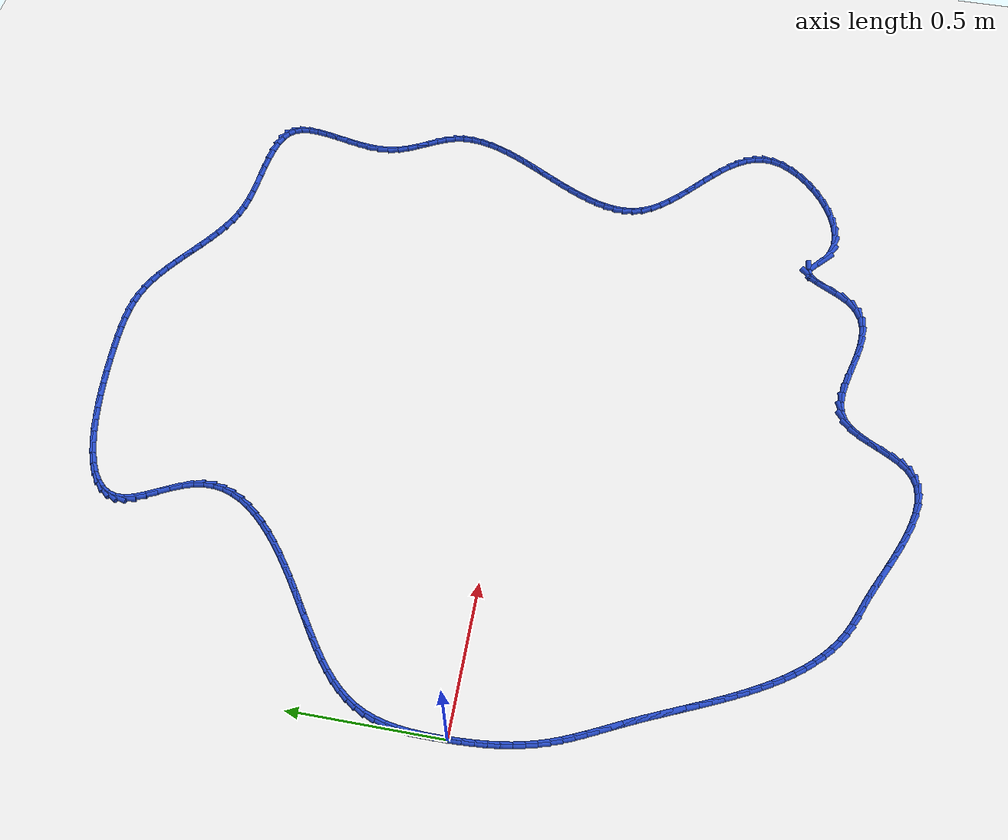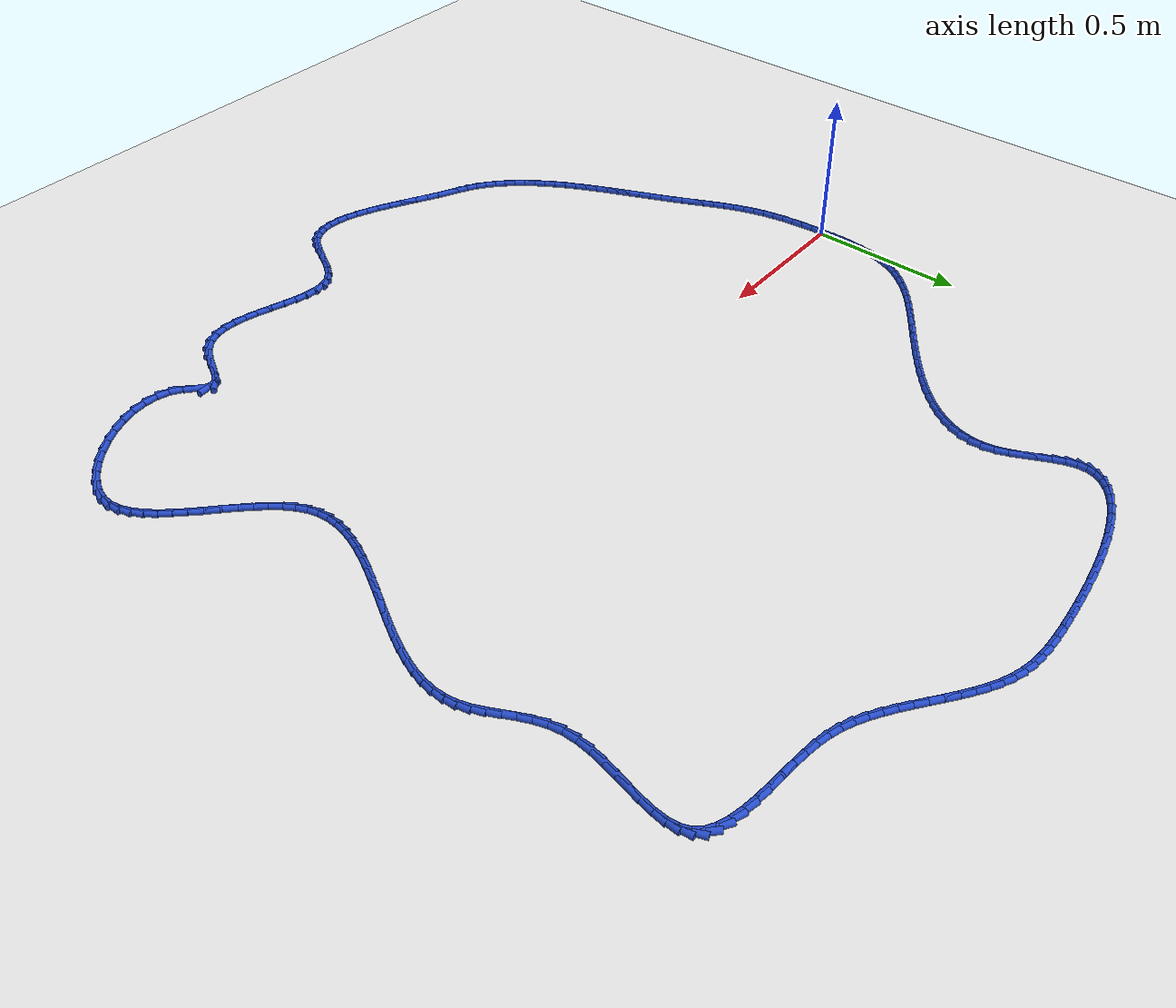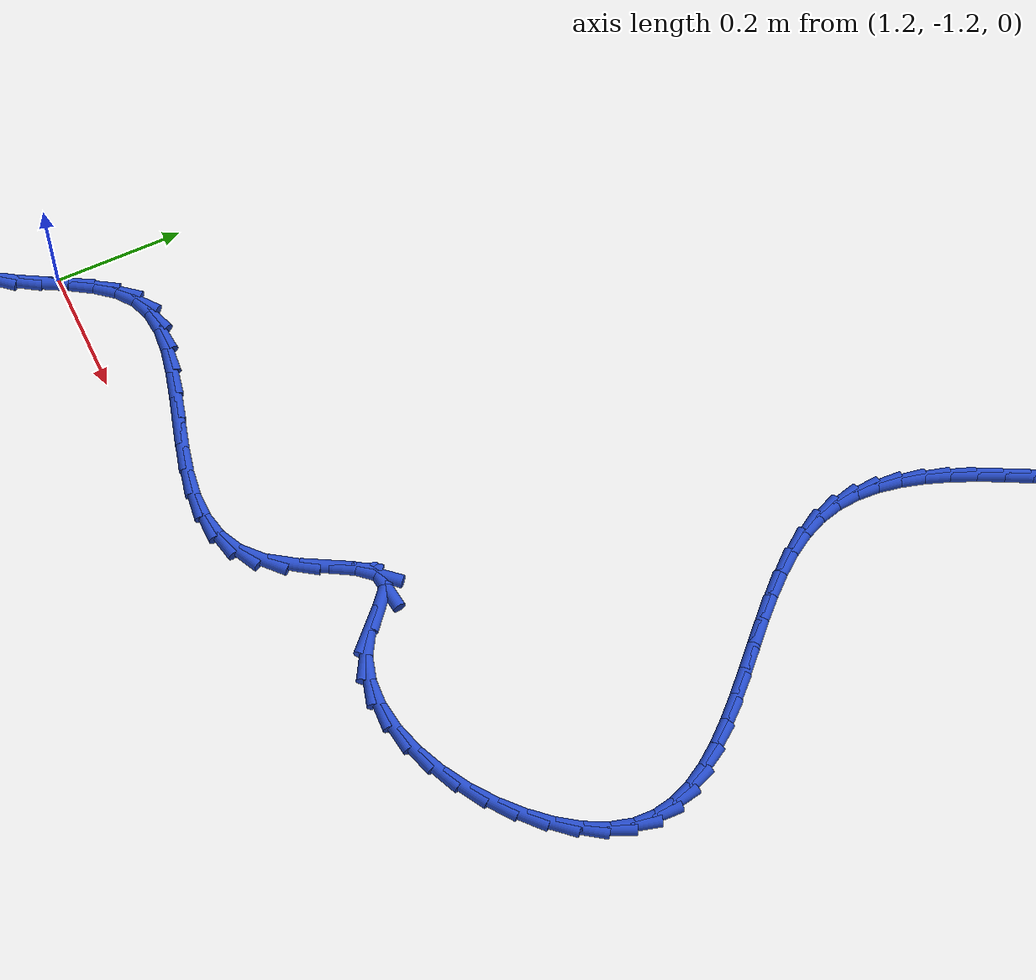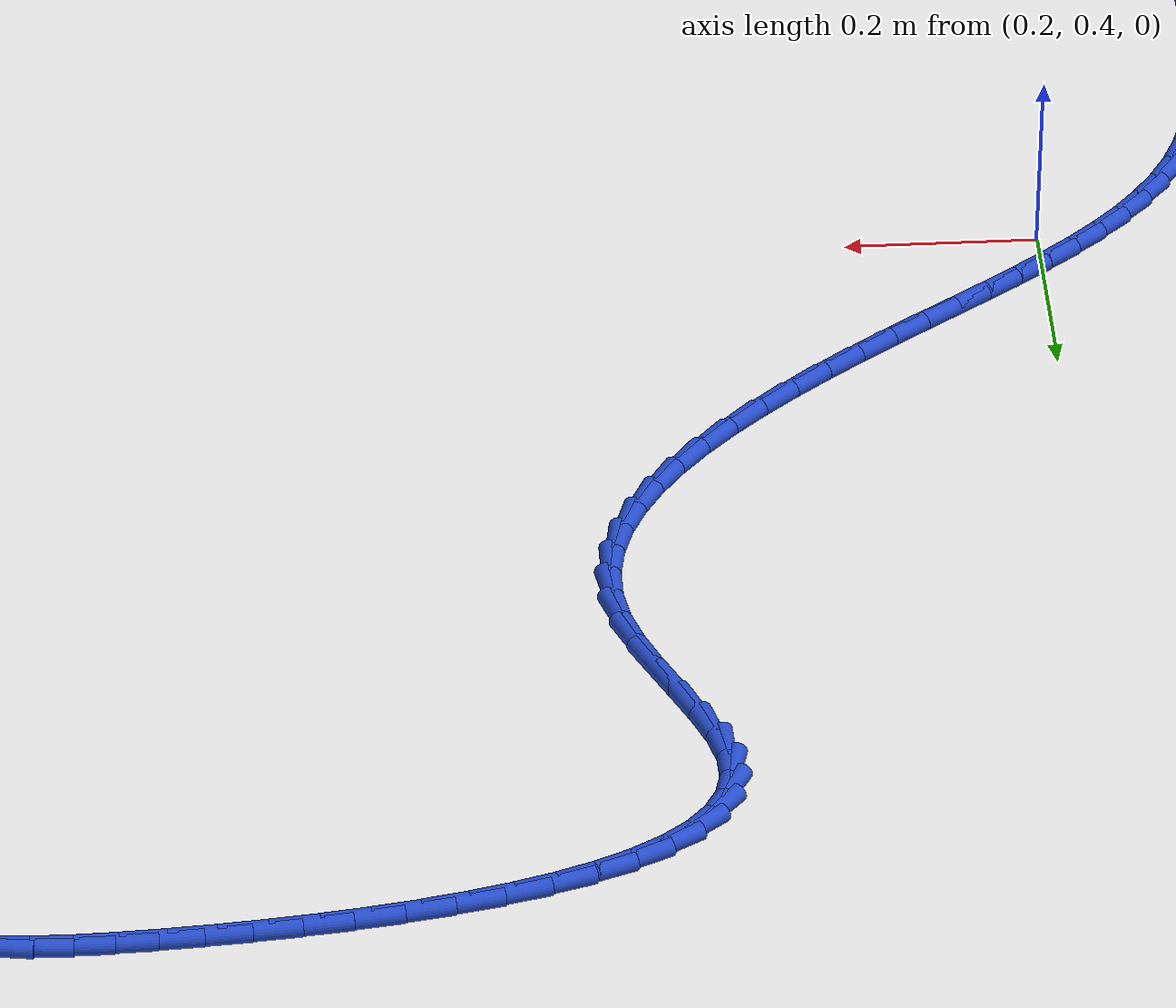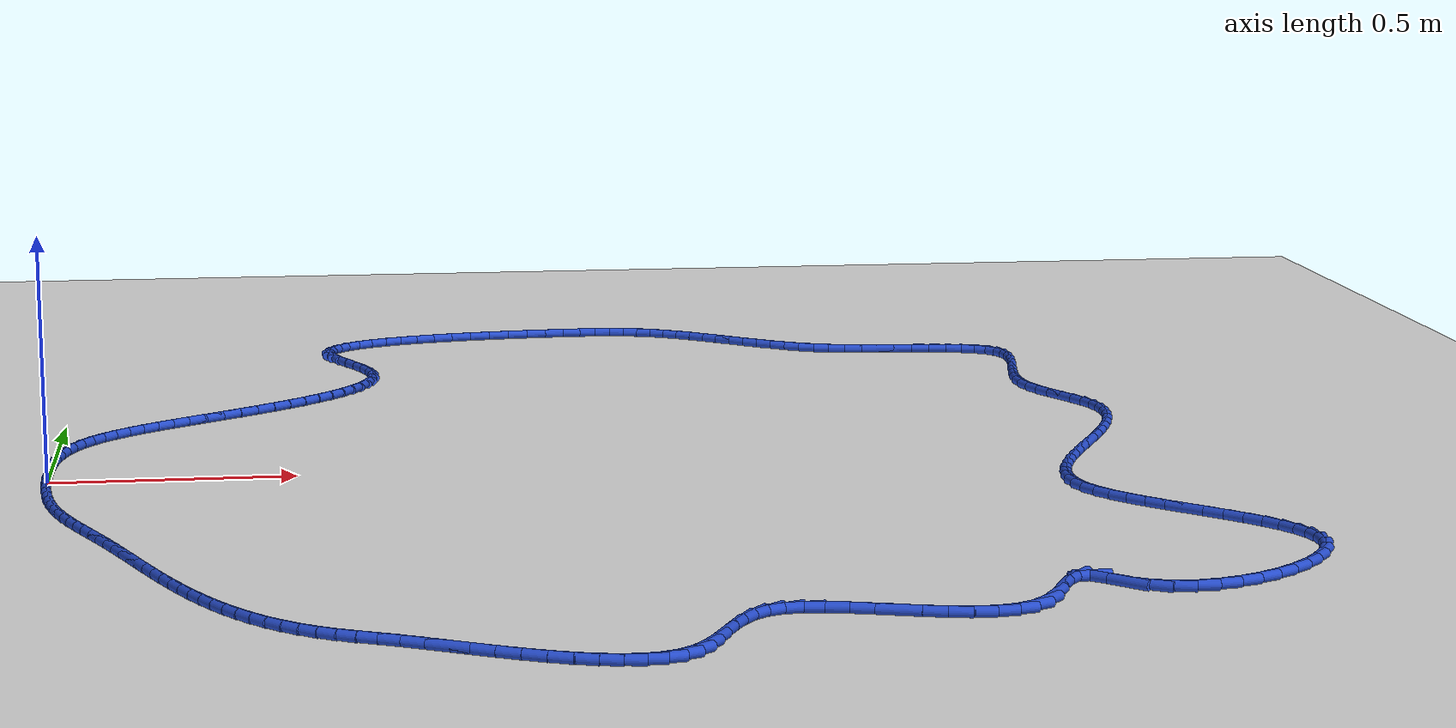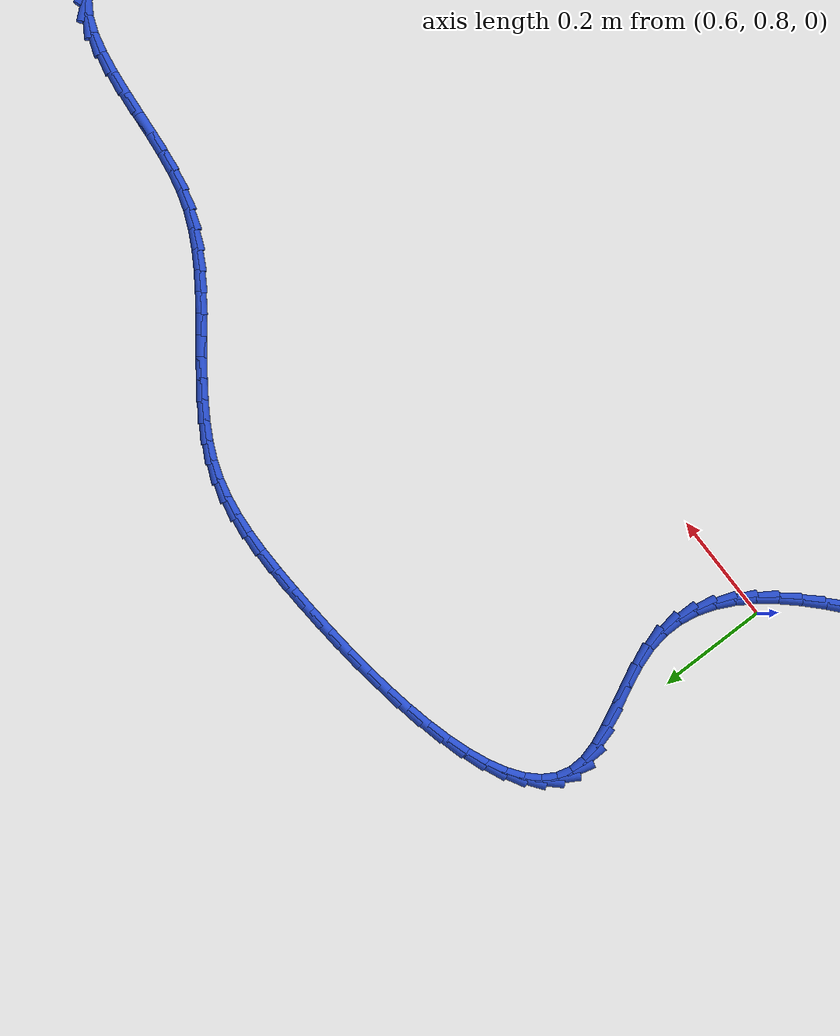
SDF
<sdf version="1.6">
 <world name="default">
  <light name="sun" type="directional">
   <pose>0 0 10 0 -0 0</pose>
   <diffuse>0.8 0.8 0.8 1</diffuse>
   <specular>0.2 0.2 0.2 1</specular>
   <attenuation>
    <range>1000</range>
    <constant>0.9</constant>
    <linear>0.01</linear>
    <quadratic>0.001</quadratic>
   </attenuation>
   <direction>-0.5 0.1 -0.9</direction>
  </light>
  <model name="ground_plane">
   <static>1</static>
   <link name="link">
    <collision name="collision">
     <geometry><plane><normal>0 0 1</normal><size>100 100</size></plane></geometry>
     <surface><friction><ode><mu>100</mu><mu2>50</mu2></ode></friction></surface>
    </collision>
    <visual name="visual">
     <cast_shadows>0</cast_shadows>
     <geometry><plane><normal>0 0 1</normal><size>100 100</size></plane></geometry>
     <material>
      <script><uri>file://media/materials/scripts/gazebo.material</uri><name>Gazebo/WhiteGlow</name></script>
     </material>
    </visual>
   </link>
  </model>
  <gravity>0 0 -9.8</gravity>
  <magnetic_field>6e-06 2.3e-05 -4.2e-05</magnetic_field>
  <atmosphere type="adiabatic"/>
  <physics name="default_physics" default="0" type="ode">
   <max_step_size>0.001</max_step_size>
   <real_time_factor>1</real_time_factor>
   <real_time_update_rate>1000</real_time_update_rate>
  </physics>
  <scene><ambient>0.4 0.4 0.4 1</ambient><background>0.7 0.7 0.7 1</background><shadows>1</shadows></scene>
  <spherical_coordinates>
   <surface_model>EARTH_WGS84</surface_model>
   <latitude_deg>0</latitude_deg>
   <longitude_deg>0</longitude_deg>
   <elevation>0</elevation>
   <heading_deg>0</heading_deg>
  </spherical_coordinates>
  <model name="line">
   <link name="link_0">
    <pose>2.0599841277224584e-17 -2.0816681711721685e-17 0.01 0 1.57 -1.5588604875989553</pose>
    <collision name="collision">
     <geometry><cylinder><radius>0.01</radius><length>0.08</length></cylinder></geometry>
    </collision>
    <visual name="visual">
     <material>
      <script><name>Gazebo/Blue</name><uri>file://media/materials/scripts/gazebo.material</uri></script>
     </material>
     <geometry><cylinder><radius>0.01</radius><length>0.08</length></cylinder></geometry>
    </visual>
   </link>
   <link name="link_1">
    <pose>-0.00046476527579154836 0.038936785016901176 0.01 0 1.57 1.5537833931867555</pose>
    <collision name="collision">
     <geometry><cylinder><radius>0.01</radius><length>0.08</length></cylinder></geometry>
    </collision>
    <visual name="visual">
     <material>
      <script><name>Gazebo/Blue</name><uri>file://media/materials/scripts/gazebo.material</uri></script>
     </material>
     <geometry><cylinder><radius>0.01</radius><length>0.08</length></cylinder></geometry>
    </visual>
   </link>
   <link name="link_2">
    <pose>0.00019843336409469333 0.07791505111378115 0.01 0 1.57 1.5151328518593705</pose>
    <collision name="collision">
     <geometry><cylinder><radius>0.01</radius><length>0.08</length></cylinder></geometry>
    </collision>
    <visual name="visual">
     <material>
      <script><name>Gazebo/Blue</name><uri>file://media/materials/scripts/gazebo.material</uri></script>
     </material>
     <geometry><cylinder><radius>0.01</radius><length>0.08</length></cylinder></geometry>
    </visual>
   </link>
   <link name="link_3">
    <pose>0.0023521172330233805 0.1165662325395032 0.01 0 1.57 1.4656230836972577</pose>
    <collision name="collision">
     <geometry><cylinder><radius>0.01</radius><length>0.08</length></cylinder></geometry>
    </collision>
    <visual name="visual">
     <material>
      <script><name>Gazebo/Blue</name><uri>file://media/materials/scripts/gazebo.material</uri></script>
     </material>
     <geometry><cylinder><radius>0.01</radius><length>0.08</length></cylinder></geometry>
    </visual>
   </link>
   <link name="link_4">
    <pose>0.00635880764435914 0.15452176354293048 0.01 0 1.57 1.4037054161835596</pose>
    <collision name="collision">
     <geometry><cylinder><radius>0.01</radius><length>0.08</length></cylinder></geometry>
    </collision>
    <visual name="visual">
     <material>
      <script><name>Gazebo/Blue</name><uri>file://media/materials/scripts/gazebo.material</uri></script>
     </material>
     <geometry><cylinder><radius>0.01</radius><length>0.08</length></cylinder></geometry>
    </visual>
   </link>
   <link name="link_5">
    <pose>0.01258102591146661 0.19141307837292645 0.01 0 1.57 1.3275268543399565</pose>
    <collision name="collision">
     <geometry><cylinder><radius>0.01</radius><length>0.08</length></cylinder></geometry>
    </collision>
    <visual name="visual">
     <material>
      <script><name>Gazebo/Blue</name><uri>file://media/materials/scripts/gazebo.material</uri></script>
     </material>
     <geometry><cylinder><radius>0.01</radius><length>0.08</length></cylinder></geometry>
    </visual>
   </link>
   <link name="link_6">
    <pose>0.021381293347710426 0.22687161127835437 0.01 0 1.57 1.2351588532015916</pose>
    <collision name="collision">
     <geometry><cylinder><radius>0.01</radius><length>0.08</length></cylinder></geometry>
    </collision>
    <visual name="visual">
     <material>
      <script><name>Gazebo/Blue</name><uri>file://media/materials/scripts/gazebo.material</uri></script>
     </material>
     <geometry><cylinder><radius>0.01</radius><length>0.08</length></cylinder></geometry>
    </visual>
   </link>
   <link name="link_7">
    <pose>0.0331221312664552 0.2605287965080773 0.01 0 1.57 1.1265397133975918</pose>
    <collision name="collision">
     <geometry><cylinder><radius>0.01</radius><length>0.08</length></cylinder></geometry>
    </collision>
    <visual name="visual">
     <material>
      <script><name>Gazebo/Blue</name><uri>file://media/materials/scripts/gazebo.material</uri></script>
     </material>
     <geometry><cylinder><radius>0.01</radius><length>0.08</length></cylinder></geometry>
    </visual>
   </link>
   <link name="link_8">
    <pose>0.04812858342493951 0.2920555509317611 0.01 0 1.57 1.0166711648356797</pose>
    <collision name="collision">
     <geometry><cylinder><radius>0.01</radius><length>0.08</length></cylinder></geometry>
    </collision>
    <visual name="visual">
     <material>
      <script><name>Gazebo/Blue</name><uri>file://media/materials/scripts/gazebo.material</uri></script>
     </material>
     <geometry><cylinder><radius>0.01</radius><length>0.08</length></cylinder></geometry>
    </visual>
   </link>
   <link name="link_9">
    <pose>0.06635615919485469 0.3215120960463239 0.01 0 1.57 0.9171325374831599</pose>
    <collision name="collision">
     <geometry><cylinder><radius>0.01</radius><length>0.08</length></cylinder></geometry>
    </collision>
    <visual name="visual">
     <material>
      <script><name>Gazebo/Blue</name><uri>file://media/materials/scripts/gazebo.material</uri></script>
     </material>
     <geometry><cylinder><radius>0.01</radius><length>0.08</length></cylinder></geometry>
    </visual>
   </link>
   <link name="link_10">
    <pose>0.0875500178464192 0.34918025726715307 0.01 0 1.57 0.830533037246155</pose>
    <collision name="collision">
     <geometry><cylinder><radius>0.01</radius><length>0.08</length></cylinder></geometry>
    </collision>
    <visual name="visual">
     <material>
      <script><name>Gazebo/Blue</name><uri>file://media/materials/scripts/gazebo.material</uri></script>
     </material>
     <geometry><cylinder><radius>0.01</radius><length>0.08</length></cylinder></geometry>
    </visual>
   </link>
   <link name="link_11">
    <pose>0.11145288228678281 0.3753444267191318 0.01 0 1.57 0.757918798835166</pose>
    <collision name="collision">
     <geometry><cylinder><radius>0.01</radius><length>0.08</length></cylinder></geometry>
    </collision>
    <visual name="visual">
     <material>
      <script><name>Gazebo/Blue</name><uri>file://media/materials/scripts/gazebo.material</uri></script>
     </material>
     <geometry><cylinder><radius>0.01</radius><length>0.08</length></cylinder></geometry>
    </visual>
   </link>
   <link name="link_12">
    <pose>0.13780747542309502 0.4002889965271433 0.01 0 1.57 0.6992379546814061</pose>
    <collision name="collision">
     <geometry><cylinder><radius>0.01</radius><length>0.08</length></cylinder></geometry>
    </collision>
    <visual name="visual">
     <material>
      <script><name>Gazebo/Blue</name><uri>file://media/materials/scripts/gazebo.material</uri></script>
     </material>
     <geometry><cylinder><radius>0.01</radius><length>0.08</length></cylinder></geometry>
    </visual>
   </link>
   <link name="link_13">
    <pose>0.16635652016250557 0.42429835881607064 0.01 0 1.57 0.6537888642787861</pose>
    <collision name="collision">
     <geometry><cylinder><radius>0.01</radius><length>0.08</length></cylinder></geometry>
    </collision>
    <visual name="visual">
     <material>
      <script><name>Gazebo/Blue</name><uri>file://media/materials/scripts/gazebo.material</uri></script>
     </material>
     <geometry><cylinder><radius>0.01</radius><length>0.08</length></cylinder></geometry>
    </visual>
   </link>
   <link name="link_14">
    <pose>0.19684273941216407 0.447656905710797 0.01 0 1.57 0.6205854876415965</pose>
    <collision name="collision">
     <geometry><cylinder><radius>0.01</radius><length>0.08</length></cylinder></geometry>
    </collision>
    <visual name="visual">
     <material>
      <script><name>Gazebo/Blue</name><uri>file://media/materials/scripts/gazebo.material</uri></script>
     </material>
     <geometry><cylinder><radius>0.01</radius><length>0.08</length></cylinder></geometry>
    </visual>
   </link>
   <link name="link_15">
    <pose>0.22900885607922014 0.4706490293362057 0.01 0 1.57 0.5985953012654814</pose>
    <collision name="collision">
     <geometry><cylinder><radius>0.01</radius><length>0.08</length></cylinder></geometry>
    </collision>
    <visual name="visual">
     <material>
      <script><name>Gazebo/Blue</name><uri>file://media/materials/scripts/gazebo.material</uri></script>
     </material>
     <geometry><cylinder><radius>0.01</radius><length>0.08</length></cylinder></geometry>
    </visual>
   </link>
   <link name="link_16">
    <pose>0.26259759307082353 0.4935591218171797 0.01 0 1.57 0.5868676229746435</pose>
    <collision name="collision">
     <geometry><cylinder><radius>0.01</radius><length>0.08</length></cylinder></geometry>
    </collision>
    <visual name="visual">
     <material>
      <script><name>Gazebo/Blue</name><uri>file://media/materials/scripts/gazebo.material</uri></script>
     </material>
     <geometry><cylinder><radius>0.01</radius><length>0.08</length></cylinder></geometry>
    </visual>
   </link>
   <link name="link_17">
    <pose>0.29735167329412376 0.5166715752786022 0.01 0 1.57 0.5845863753674764</pose>
    <collision name="collision">
     <geometry><cylinder><radius>0.01</radius><length>0.08</length></cylinder></geometry>
    </collision>
    <visual name="visual">
     <material>
      <script><name>Gazebo/Blue</name><uri>file://media/materials/scripts/gazebo.material</uri></script>
     </material>
     <geometry><cylinder><radius>0.01</radius><length>0.08</length></cylinder></geometry>
    </visual>
   </link>
   <link name="link_18">
    <pose>0.33301378354018724 0.5402707381035818 0.01 0 1.57 0.5905592637265834</pose>
    <collision name="collision">
     <geometry><cylinder><radius>0.01</radius><length>0.08</length></cylinder></geometry>
    </collision>
    <visual name="visual">
     <material>
      <script><name>Gazebo/Blue</name><uri>file://media/materials/scripts/gazebo.material</uri></script>
     </material>
     <geometry><cylinder><radius>0.01</radius><length>0.08</length></cylinder></geometry>
    </visual>
   </link>
   <link name="link_19">
    <pose>0.3692760568378916 0.5645797307935382 0.01 0 1.57 0.602876033827019</pose>
    <collision name="collision">
     <geometry><cylinder><radius>0.01</radius><length>0.08</length></cylinder></geometry>
    </collision>
    <visual name="visual">
     <material>
      <script><name>Gazebo/Blue</name><uri>file://media/materials/scripts/gazebo.material</uri></script>
     </material>
     <geometry><cylinder><radius>0.01</radius><length>0.08</length></cylinder></geometry>
    </visual>
   </link>
   <link name="link_20">
    <pose>0.4056795610236409 0.5896387121605603 0.01 0 1.57 0.6213430544188908</pose>
    <collision name="collision">
     <geometry><cylinder><radius>0.01</radius><length>0.08</length></cylinder></geometry>
    </collision>
    <visual name="visual">
     <material>
      <script><name>Gazebo/Blue</name><uri>file://media/materials/scripts/gazebo.material</uri></script>
     </material>
     <geometry><cylinder><radius>0.01</radius><length>0.08</length></cylinder></geometry>
    </visual>
   </link>
   <link name="link_21">
    <pose>0.44173726929301044 0.6154538143633236 0.01 0 1.57 0.6463781326160475</pose>
    <collision name="collision">
     <geometry><cylinder><radius>0.01</radius><length>0.08</length></cylinder></geometry>
    </collision>
    <visual name="visual">
     <material>
      <script><name>Gazebo/Blue</name><uri>file://media/materials/scripts/gazebo.material</uri></script>
     </material>
     <geometry><cylinder><radius>0.01</radius><length>0.08</length></cylinder></geometry>
    </visual>
   </link>
   <link name="link_22">
    <pose>0.47696215484157556 0.6420311695605039 0.01 0 1.57 0.6787155548486374</pose>
    <collision name="collision">
     <geometry><cylinder><radius>0.01</radius><length>0.08</length></cylinder></geometry>
    </collision>
    <visual name="visual">
     <material>
      <script><name>Gazebo/Blue</name><uri>file://media/materials/scripts/gazebo.material</uri></script>
     </material>
     <geometry><cylinder><radius>0.01</radius><length>0.08</length></cylinder></geometry>
    </visual>
   </link>
   <link name="link_23">
    <pose>0.5108671908649117 0.6693769099107765 0.01 0 1.57 0.7194360996943119</pose>
    <collision name="collision">
     <geometry><cylinder><radius>0.01</radius><length>0.08</length></cylinder></geometry>
    </collision>
    <visual name="visual">
     <material>
      <script><name>Gazebo/Blue</name><uri>file://media/materials/scripts/gazebo.material</uri></script>
     </material>
     <geometry><cylinder><radius>0.01</radius><length>0.08</length></cylinder></geometry>
    </visual>
   </link>
   <link name="link_24">
    <pose>0.5429653505585941 0.6974971675728168 0.01 0 1.57 0.770011473713023</pose>
    <collision name="collision">
     <geometry><cylinder><radius>0.01</radius><length>0.08</length></cylinder></geometry>
    </collision>
    <visual name="visual">
     <material>
      <script><name>Gazebo/Blue</name><uri>file://media/materials/scripts/gazebo.material</uri></script>
     </material>
     <geometry><cylinder><radius>0.01</radius><length>0.08</length></cylinder></geometry>
    </visual>
   </link>
   <link name="link_25">
    <pose>0.5727696071181978 0.7263980747053 0.01 0 1.57 0.8323450291786604</pose>
    <collision name="collision">
     <geometry><cylinder><radius>0.01</radius><length>0.08</length></cylinder></geometry>
    </collision>
    <visual name="visual">
     <material>
      <script><name>Gazebo/Blue</name><uri>file://media/materials/scripts/gazebo.material</uri></script>
     </material>
     <geometry><cylinder><radius>0.01</radius><length>0.08</length></cylinder></geometry>
    </visual>
   </link>
   <link name="link_26">
    <pose>0.5997929337392987 0.7560857634669025 0.01 0 1.57 0.908767914872844</pose>
    <collision name="collision">
     <geometry><cylinder><radius>0.01</radius><length>0.08</length></cylinder></geometry>
    </collision>
    <visual name="visual">
     <material>
      <script><name>Gazebo/Blue</name><uri>file://media/materials/scripts/gazebo.material</uri></script>
     </material>
     <geometry><cylinder><radius>0.01</radius><length>0.08</length></cylinder></geometry>
    </visual>
   </link>
   <link name="link_27">
    <pose>0.6235483036174716 0.7865663660162989 0.01 0 1.57 1.0019048405353337</pose>
    <collision name="collision">
     <geometry><cylinder><radius>0.01</radius><length>0.08</length></cylinder></geometry>
    </collision>
    <visual name="visual">
     <material>
      <script><name>Gazebo/Blue</name><uri>file://media/materials/scripts/gazebo.material</uri></script>
     </material>
     <geometry><cylinder><radius>0.01</radius><length>0.08</length></cylinder></geometry>
    </visual>
   </link>
   <link name="link_28">
    <pose>0.6435486899482923 0.8178460145121653 0.01 0 1.57 1.1142559251627124</pose>
    <collision name="collision">
     <geometry><cylinder><radius>0.01</radius><length>0.08</length></cylinder></geometry>
    </collision>
    <visual name="visual">
     <material>
      <script><name>Gazebo/Blue</name><uri>file://media/materials/scripts/gazebo.material</uri></script>
     </material>
     <geometry><cylinder><radius>0.01</radius><length>0.08</length></cylinder></geometry>
    </visual>
   </link>
   <link name="link_29">
    <pose>0.6593070659273356 0.8499308411131764 0.01 0 1.57 1.2472969267548355</pose>
    <collision name="collision">
     <geometry><cylinder><radius>0.01</radius><length>0.08</length></cylinder></geometry>
    </collision>
    <visual name="visual">
     <material>
      <script><name>Gazebo/Blue</name><uri>file://media/materials/scripts/gazebo.material</uri></script>
     </material>
     <geometry><cylinder><radius>0.01</radius><length>0.08</length></cylinder></geometry>
    </visual>
   </link>
   <link name="link_30">
    <pose>0.6703364047501773 0.8828269779780086 0.01 0 1.57 1.4000441554039906</pose>
    <collision name="collision">
     <geometry><cylinder><radius>0.01</radius><length>0.08</length></cylinder></geometry>
    </collision>
    <visual name="visual">
     <material>
      <script><name>Gazebo/Blue</name><uri>file://media/materials/scripts/gazebo.material</uri></script>
     </material>
     <geometry><cylinder><radius>0.01</radius><length>0.08</length></cylinder></geometry>
    </visual>
   </link>
   <link name="link_31">
    <pose>0.6761496796123925 0.9165405572653367 0.01 0 1.57 1.5676060313882123</pose>
    <collision name="collision">
     <geometry><cylinder><radius>0.01</radius><length>0.08</length></cylinder></geometry>
    </collision>
    <visual name="visual">
     <material>
      <script><name>Gazebo/Blue</name><uri>file://media/materials/scripts/gazebo.material</uri></script>
     </material>
     <geometry><cylinder><radius>0.01</radius><length>0.08</length></cylinder></geometry>
    </visual>
   </link>
   <link name="link_32">
    <pose>0.6762598637095567 0.9510777111338368 0.01 0 1.57 -1.4005545198780656</pose>
    <collision name="collision">
     <geometry><cylinder><radius>0.01</radius><length>0.08</length></cylinder></geometry>
    </collision>
    <visual name="visual">
     <material>
      <script><name>Gazebo/Blue</name><uri>file://media/materials/scripts/gazebo.material</uri></script>
     </material>
     <geometry><cylinder><radius>0.01</radius><length>0.08</length></cylinder></geometry>
    </visual>
   </link>
   <link name="link_33">
    <pose>0.6701801022839958 0.9864445380836312 0.01 0 1.57 -1.2456048604465702</pose>
    <collision name="collision">
     <geometry><cylinder><radius>0.01</radius><length>0.08</length></cylinder></geometry>
    </collision>
    <visual name="visual">
     <material>
      <script><name>Gazebo/Blue</name><uri>file://media/materials/scripts/gazebo.material</uri></script>
     </material>
     <geometry><cylinder><radius>0.01</radius><length>0.08</length></cylinder></geometry>
    </visual>
   </link>
   <link name="link_34">
    <pose>0.6580128716791604 1.0225318421855312 0.01 0 1.57 -1.1502628188703683</pose>
    <collision name="collision">
     <geometry><cylinder><radius>0.01</radius><length>0.08</length></cylinder></geometry>
    </collision>
    <visual name="visual">
     <material>
      <script><name>Gazebo/Blue</name><uri>file://media/materials/scripts/gazebo.material</uri></script>
     </material>
     <geometry><cylinder><radius>0.01</radius><length>0.08</length></cylinder></geometry>
    </visual>
   </link>
   <link name="link_35">
    <pose>0.6417676468936827 1.0588573497596132 0.01 0 1.57 -1.1088017217124908</pose>
    <collision name="collision">
     <geometry><cylinder><radius>0.01</radius><length>0.08</length></cylinder></geometry>
    </collision>
    <visual name="visual">
     <material>
      <script><name>Gazebo/Blue</name><uri>file://media/materials/scripts/gazebo.material</uri></script>
     </material>
     <geometry><cylinder><radius>0.01</radius><length>0.08</length></cylinder></geometry>
    </visual>
   </link>
   <link name="link_36">
    <pose>0.623838926941341 1.0948634625350504 0.01 0 1.57 -1.1150785877863905</pose>
    <collision name="collision">
     <geometry><cylinder><radius>0.01</radius><length>0.08</length></cylinder></geometry>
    </collision>
    <visual name="visual">
     <material>
      <script><name>Gazebo/Blue</name><uri>file://media/materials/scripts/gazebo.material</uri></script>
     </material>
     <geometry><cylinder><radius>0.01</radius><length>0.08</length></cylinder></geometry>
    </visual>
   </link>
   <link name="link_37">
    <pose>0.6066212108359131 1.1299925822410182 0.01 0 1.57 -1.1741649784683754</pose>
    <collision name="collision">
     <geometry><cylinder><radius>0.01</radius><length>0.08</length></cylinder></geometry>
    </collision>
    <visual name="visual">
     <material>
      <script><name>Gazebo/Blue</name><uri>file://media/materials/scripts/gazebo.material</uri></script>
     </material>
     <geometry><cylinder><radius>0.01</radius><length>0.08</length></cylinder></geometry>
    </visual>
   </link>
   <link name="link_38">
    <pose>0.5925089975911786 1.1636871106066904 0.01 0 1.57 -1.3055392816997946</pose>
    <collision name="collision">
     <geometry><cylinder><radius>0.01</radius><length>0.08</length></cylinder></geometry>
    </collision>
    <visual name="visual">
     <material>
      <script><name>Gazebo/Blue</name><uri>file://media/materials/scripts/gazebo.material</uri></script>
     </material>
     <geometry><cylinder><radius>0.01</radius><length>0.08</length></cylinder></geometry>
    </visual>
   </link>
   <link name="link_39">
    <pose>0.5838967862209155 1.1953894493612418 0.01 0 1.57 -1.53804504952124</pose>
    <collision name="collision">
     <geometry><cylinder><radius>0.01</radius><length>0.08</length></cylinder></geometry>
    </collision>
    <visual name="visual">
     <material>
      <script><name>Gazebo/Blue</name><uri>file://media/materials/scripts/gazebo.material</uri></script>
     </material>
     <geometry><cylinder><radius>0.01</radius><length>0.08</length></cylinder></geometry>
    </visual>
   </link>
   <link name="link_40">
    <pose>0.5829399467591998 1.2245943354037192 0.01 0 1.57 1.3158878228113873</pose>
    <collision name="collision">
     <geometry><cylinder><radius>0.01</radius><length>0.08</length></cylinder></geometry>
    </collision>
    <visual name="visual">
     <material>
      <script><name>Gazebo/Blue</name><uri>file://media/materials/scripts/gazebo.material</uri></script>
     </material>
     <geometry><cylinder><radius>0.01</radius><length>0.08</length></cylinder></geometry>
    </visual>
   </link>
   <link name="link_41">
    <pose>0.5898769505430752 1.2512160332833222 0.01 0 1.57 1.0409371398055502</pose>
    <collision name="collision">
     <geometry><cylinder><radius>0.01</radius><length>0.08</length></cylinder></geometry>
    </collision>
    <visual name="visual">
     <material>
      <script><name>Gazebo/Blue</name><uri>file://media/materials/scripts/gazebo.material</uri></script>
     </material>
     <geometry><cylinder><radius>0.01</radius><length>0.08</length></cylinder></geometry>
    </visual>
   </link>
   <link name="link_42">
    <pose>0.6040248727348425 1.275370462009472 0.01 0 1.57 0.8120974211857578</pose>
    <collision name="collision">
     <geometry><cylinder><radius>0.01</radius><length>0.08</length></cylinder></geometry>
    </collision>
    <visual name="visual">
     <material>
      <script><name>Gazebo/Blue</name><uri>file://media/materials/scripts/gazebo.material</uri></script>
     </material>
     <geometry><cylinder><radius>0.01</radius><length>0.08</length></cylinder></geometry>
    </visual>
   </link>
   <link name="link_43">
    <pose>0.6246949288013218 1.2971748230298725 0.01 0 1.57 0.6360693798284879</pose>
    <collision name="collision">
     <geometry><cylinder><radius>0.01</radius><length>0.08</length></cylinder></geometry>
    </collision>
    <visual name="visual">
     <material>
      <script><name>Gazebo/Blue</name><uri>file://media/materials/scripts/gazebo.material</uri></script>
     </material>
     <geometry><cylinder><radius>0.01</radius><length>0.08</length></cylinder></geometry>
    </visual>
   </link>
   <link name="link_44">
    <pose>0.6511983342093335 1.3167463177922294 0.01 0 1.57 0.5040419477916969</pose>
    <collision name="collision">
     <geometry><cylinder><radius>0.01</radius><length>0.08</length></cylinder></geometry>
    </collision>
    <visual name="visual">
     <material>
      <script><name>Gazebo/Blue</name><uri>file://media/materials/scripts/gazebo.material</uri></script>
     </material>
     <geometry><cylinder><radius>0.01</radius><length>0.08</length></cylinder></geometry>
    </visual>
   </link>
   <link name="link_45">
    <pose>0.6828463044256973 1.3342021477442465 0.01 0 1.57 0.4045250662987084</pose>
    <collision name="collision">
     <geometry><cylinder><radius>0.01</radius><length>0.08</length></cylinder></geometry>
    </collision>
    <visual name="visual">
     <material>
      <script><name>Gazebo/Blue</name><uri>file://media/materials/scripts/gazebo.material</uri></script>
     </material>
     <geometry><cylinder><radius>0.01</radius><length>0.08</length></cylinder></geometry>
    </visual>
   </link>
   <link name="link_46">
    <pose>0.7189500549172332 1.349659514333629 0.01 0 1.57 0.3281892255106754</pose>
    <collision name="collision">
     <geometry><cylinder><radius>0.01</radius><length>0.08</length></cylinder></geometry>
    </collision>
    <visual name="visual">
     <material>
      <script><name>Gazebo/Blue</name><uri>file://media/materials/scripts/gazebo.material</uri></script>
     </material>
     <geometry><cylinder><radius>0.01</radius><length>0.08</length></cylinder></geometry>
    </visual>
   </link>
   <link name="link_47">
    <pose>0.7588208011507614 1.3632356190080817 0.01 0 1.57 0.26838960862168726</pose>
    <collision name="collision">
     <geometry><cylinder><radius>0.01</radius><length>0.08</length></cylinder></geometry>
    </collision>
    <visual name="visual">
     <material>
      <script><name>Gazebo/Blue</name><uri>file://media/materials/scripts/gazebo.material</uri></script>
     </material>
     <geometry><cylinder><radius>0.01</radius><length>0.08</length></cylinder></geometry>
    </visual>
   </link>
   <link name="link_48">
    <pose>0.8017697585931022 1.3750476632153095 0.01 0 1.57 0.22055956956595446</pose>
    <collision name="collision">
     <geometry><cylinder><radius>0.01</radius><length>0.08</length></cylinder></geometry>
    </collision>
    <visual name="visual">
     <material>
      <script><name>Gazebo/Blue</name><uri>file://media/materials/scripts/gazebo.material</uri></script>
     </material>
     <geometry><cylinder><radius>0.01</radius><length>0.08</length></cylinder></geometry>
    </visual>
   </link>
   <link name="link_49">
    <pose>0.8471081427110748 1.3852128484030168 0.01 0 1.57 0.1815605313615968</pose>
    <collision name="collision">
     <geometry><cylinder><radius>0.01</radius><length>0.08</length></cylinder></geometry>
    </collision>
    <visual name="visual">
     <material>
      <script><name>Gazebo/Blue</name><uri>file://media/materials/scripts/gazebo.material</uri></script>
     </material>
     <geometry><cylinder><radius>0.01</radius><length>0.08</length></cylinder></geometry>
    </visual>
   </link>
   <link name="link_50">
    <pose>0.8941471689715003 1.393848376018909 0.01 0 1.57 0.14920416592148056</pose>
    <collision name="collision">
     <geometry><cylinder><radius>0.01</radius><length>0.08</length></cylinder></geometry>
    </collision>
    <visual name="visual">
     <material>
      <script><name>Gazebo/Blue</name><uri>file://media/materials/scripts/gazebo.material</uri></script>
     </material>
     <geometry><cylinder><radius>0.01</radius><length>0.08</length></cylinder></geometry>
    </visual>
   </link>
   <link name="link_51">
    <pose>0.9421980528411982 1.4010714475106905 0.01 0 1.57 0.12193358092339436</pose>
    <collision name="collision">
     <geometry><cylinder><radius>0.01</radius><length>0.08</length></cylinder></geometry>
    </collision>
    <visual name="visual">
     <material>
      <script><name>Gazebo/Blue</name><uri>file://media/materials/scripts/gazebo.material</uri></script>
     </material>
     <geometry><cylinder><radius>0.01</radius><length>0.08</length></cylinder></geometry>
    </visual>
   </link>
   <link name="link_52">
    <pose>0.9905720097869887 1.406999264326066 0.01 0 1.57 0.0986154852021085</pose>
    <collision name="collision">
     <geometry><cylinder><radius>0.01</radius><length>0.08</length></cylinder></geometry>
    </collision>
    <visual name="visual">
     <material>
      <script><name>Gazebo/Blue</name><uri>file://media/materials/scripts/gazebo.material</uri></script>
     </material>
     <geometry><cylinder><radius>0.01</radius><length>0.08</length></cylinder></geometry>
    </visual>
   </link>
   <link name="link_53">
    <pose>1.0385802552756918 1.4117490279127405 0.01 0 1.57 0.07840374802057481</pose>
    <collision name="collision">
     <geometry><cylinder><radius>0.01</radius><length>0.08</length></cylinder></geometry>
    </collision>
    <visual name="visual">
     <material>
      <script><name>Gazebo/Blue</name><uri>file://media/materials/scripts/gazebo.material</uri></script>
     </material>
     <geometry><cylinder><radius>0.01</radius><length>0.08</length></cylinder></geometry>
    </visual>
   </link>
   <link name="link_54">
    <pose>1.0855340047741273 1.4154379397184185 0.01 0 1.57 0.060647344001718215</pose>
    <collision name="collision">
     <geometry><cylinder><radius>0.01</radius><length>0.08</length></cylinder></geometry>
    </collision>
    <visual name="visual">
     <material>
      <script><name>Gazebo/Blue</name><uri>file://media/materials/scripts/gazebo.material</uri></script>
     </material>
     <geometry><cylinder><radius>0.01</radius><length>0.08</length></cylinder></geometry>
    </visual>
   </link>
   <link name="link_55">
    <pose>1.130744473749116 1.418183201190805 0.01 0 1.57 0.04356480185510023</pose>
    <collision name="collision">
     <geometry><cylinder><radius>0.01</radius><length>0.08</length></cylinder></geometry>
    </collision>
    <visual name="visual">
     <material>
      <script><name>Gazebo/Blue</name><uri>file://media/materials/scripts/gazebo.material</uri></script>
     </material>
     <geometry><cylinder><radius>0.01</radius><length>0.08</length></cylinder></geometry>
    </visual>
   </link>
   <link name="link_56">
    <pose>1.1736143919096131 1.4200520030919936 0.01 0 1.57 0.017813120627240837</pose>
    <collision name="collision">
     <geometry><cylinder><radius>0.01</radius><length>0.08</length></cylinder></geometry>
    </collision>
    <visual name="visual">
     <material>
      <script><name>Gazebo/Blue</name><uri>file://media/materials/scripts/gazebo.material</uri></script>
     </material>
     <geometry><cylinder><radius>0.01</radius><length>0.08</length></cylinder></geometry>
    </visual>
   </link>
   <link name="link_57">
    <pose>1.214163440559218 1.4207743845941585 0.01 0 1.57 -0.021638825132130456</pose>
    <collision name="collision">
     <geometry><cylinder><radius>0.01</radius><length>0.08</length></cylinder></geometry>
    </collision>
    <visual name="visual">
     <material>
      <script><name>Gazebo/Blue</name><uri>file://media/materials/scripts/gazebo.material</uri></script>
     </material>
     <geometry><cylinder><radius>0.01</radius><length>0.08</length></cylinder></geometry>
    </visual>
   </link>
   <link name="link_58">
    <pose>1.2526661764890905 1.4199411005615779 0.01 0 1.57 -0.07604416616218247</pose>
    <collision name="collision">
     <geometry><cylinder><radius>0.01</radius><length>0.08</length></cylinder></geometry>
    </collision>
    <visual name="visual">
     <material>
      <script><name>Gazebo/Blue</name><uri>file://media/materials/scripts/gazebo.material</uri></script>
     </material>
     <geometry><cylinder><radius>0.01</radius><length>0.08</length></cylinder></geometry>
    </visual>
   </link>
   <link name="link_59">
    <pose>1.2893979614746258 1.4171424659509002 0.01 0 1.57 -0.1457865926980805</pose>
    <collision name="collision">
     <geometry><cylinder><radius>0.01</radius><length>0.08</length></cylinder></geometry>
    </collision>
    <visual name="visual">
     <material>
      <script><name>Gazebo/Blue</name><uri>file://media/materials/scripts/gazebo.material</uri></script>
     </material>
     <geometry><cylinder><radius>0.01</radius><length>0.08</length></cylinder></geometry>
    </visual>
   </link>
   <link name="link_60">
    <pose>1.3246341572912177 1.4119687957187745 0.01 0 1.57 -0.22982657658886604</pose>
    <collision name="collision">
     <geometry><cylinder><radius>0.01</radius><length>0.08</length></cylinder></geometry>
    </collision>
    <visual name="visual">
     <material>
      <script><name>Gazebo/Blue</name><uri>file://media/materials/scripts/gazebo.material</uri></script>
     </material>
     <geometry><cylinder><radius>0.01</radius><length>0.08</length></cylinder></geometry>
    </visual>
   </link>
   <link name="link_61">
    <pose>1.3586501257142614 1.4040104048218491 0.01 0 1.57 -0.32525071271518846</pose>
    <collision name="collision">
     <geometry><cylinder><radius>0.01</radius><length>0.08</length></cylinder></geometry>
    </collision>
    <visual name="visual">
     <material>
      <script><name>Gazebo/Blue</name><uri>file://media/materials/scripts/gazebo.material</uri></script>
     </material>
     <geometry><cylinder><radius>0.01</radius><length>0.08</length></cylinder></geometry>
    </visual>
   </link>
   <link name="link_62">
    <pose>1.3917211790418753 1.392857954150063 0.01 0 1.57 -0.42168953792731234</pose>
    <collision name="collision">
     <geometry><cylinder><radius>0.01</radius><length>0.08</length></cylinder></geometry>
    </collision>
    <visual name="visual">
     <material>
      <script><name>Gazebo/Blue</name><uri>file://media/materials/scripts/gazebo.material</uri></script>
     </material>
     <geometry><cylinder><radius>0.01</radius><length>0.08</length></cylinder></geometry>
    </visual>
   </link>
   <link name="link_63">
    <pose>1.424088924020396 1.3783377657619418 0.01 0 1.57 -0.5008743759767215</pose>
    <collision name="collision">
     <geometry><cylinder><radius>0.01</radius><length>0.08</length></cylinder></geometry>
    </collision>
    <visual name="visual">
     <material>
      <script><name>Gazebo/Blue</name><uri>file://media/materials/scripts/gazebo.material</uri></script>
     </material>
     <geometry><cylinder><radius>0.01</radius><length>0.08</length></cylinder></geometry>
    </visual>
   </link>
   <link name="link_64">
    <pose>1.455902636222606 1.360921719231152 0.01 0 1.57 -0.5611075231553009</pose>
    <collision name="collision">
     <geometry><cylinder><radius>0.01</radius><length>0.08</length></cylinder></geometry>
    </collision>
    <visual name="visual">
     <material>
      <script><name>Gazebo/Blue</name><uri>file://media/materials/scripts/gazebo.material</uri></script>
     </material>
     <geometry><cylinder><radius>0.01</radius><length>0.08</length></cylinder></geometry>
    </visual>
   </link>
   <link name="link_65">
    <pose>1.4872959228110223 1.3411912439140503 0.01 0 1.57 -0.6039832337709676</pose>
    <collision name="collision">
     <geometry><cylinder><radius>0.01</radius><length>0.08</length></cylinder></geometry>
    </collision>
    <visual name="visual">
     <material>
      <script><name>Gazebo/Blue</name><uri>file://media/materials/scripts/gazebo.material</uri></script>
     </material>
     <geometry><cylinder><radius>0.01</radius><length>0.08</length></cylinder></geometry>
    </visual>
   </link>
   <link name="link_66">
    <pose>1.518402390948162 1.3197277691669929 0.01 0 1.57 -0.6309816007855725</pose>
    <collision name="collision">
     <geometry><cylinder><radius>0.01</radius><length>0.08</length></cylinder></geometry>
    </collision>
    <visual name="visual">
     <material>
      <script><name>Gazebo/Blue</name><uri>file://media/materials/scripts/gazebo.material</uri></script>
     </material>
     <geometry><cylinder><radius>0.01</radius><length>0.08</length></cylinder></geometry>
    </visual>
   </link>
   <link name="link_67">
    <pose>1.549355647796541 1.297112724346337 0.01 0 1.57 -0.6431895771016136</pose>
    <collision name="collision">
     <geometry><cylinder><radius>0.01</radius><length>0.08</length></cylinder></geometry>
    </collision>
    <visual name="visual">
     <material>
      <script><name>Gazebo/Blue</name><uri>file://media/materials/scripts/gazebo.material</uri></script>
     </material>
     <geometry><cylinder><radius>0.01</radius><length>0.08</length></cylinder></geometry>
    </visual>
   </link>
   <link name="link_68">
    <pose>1.5802893005186762 1.2739275388084388 0.01 0 1.57 -0.6411916072646232</pose>
    <collision name="collision">
     <geometry><cylinder><radius>0.01</radius><length>0.08</length></cylinder></geometry>
    </collision>
    <visual name="visual">
     <material>
      <script><name>Gazebo/Blue</name><uri>file://media/materials/scripts/gazebo.material</uri></script>
     </material>
     <geometry><cylinder><radius>0.01</radius><length>0.08</length></cylinder></geometry>
    </visual>
   </link>
   <link name="link_69">
    <pose>1.611336956277084 1.2507536419096557 0.01 0 1.57 -0.625044790131475</pose>
    <collision name="collision">
     <geometry><cylinder><radius>0.01</radius><length>0.08</length></cylinder></geometry>
    </collision>
    <visual name="visual">
     <material>
      <script><name>Gazebo/Blue</name><uri>file://media/materials/scripts/gazebo.material</uri></script>
     </material>
     <geometry><cylinder><radius>0.01</radius><length>0.08</length></cylinder></geometry>
    </visual>
   </link>
   <link name="link_70">
    <pose>1.6426322222342817 1.2281724630063429 0.01 0 1.57 -0.5943004446333864</pose>
    <collision name="collision">
     <geometry><cylinder><radius>0.01</radius><length>0.08</length></cylinder></geometry>
    </collision>
    <visual name="visual">
     <material>
      <script><name>Gazebo/Blue</name><uri>file://media/materials/scripts/gazebo.material</uri></script>
     </material>
     <geometry><cylinder><radius>0.01</radius><length>0.08</length></cylinder></geometry>
    </visual>
   </link>
   <link name="link_71">
    <pose>1.674308705552785 1.2067654314548584 0.01 0 1.57 -0.5480740448327908</pose>
    <collision name="collision">
     <geometry><cylinder><radius>0.01</radius><length>0.08</length></cylinder></geometry>
    </collision>
    <visual name="visual">
     <material>
      <script><name>Gazebo/Blue</name><uri>file://media/materials/scripts/gazebo.material</uri></script>
     </material>
     <geometry><cylinder><radius>0.01</radius><length>0.08</length></cylinder></geometry>
    </visual>
   </link>
   <link name="link_72">
    <pose>1.7065000133951111 1.187113976611558 0.01 0 1.57 -0.485201968358086</pose>
    <collision name="collision">
     <geometry><cylinder><radius>0.01</radius><length>0.08</length></cylinder></geometry>
    </collision>
    <visual name="visual">
     <material>
      <script><name>Gazebo/Blue</name><uri>file://media/materials/scripts/gazebo.material</uri></script>
     </material>
     <geometry><cylinder><radius>0.01</radius><length>0.08</length></cylinder></geometry>
    </visual>
   </link>
   <link name="link_73">
    <pose>1.7393397529237764 1.169799527832799 0.01 0 1.57 -0.40455703558338546</pose>
    <collision name="collision">
     <geometry><cylinder><radius>0.01</radius><length>0.08</length></cylinder></geometry>
    </collision>
    <visual name="visual">
     <material>
      <script><name>Gazebo/Blue</name><uri>file://media/materials/scripts/gazebo.material</uri></script>
     </material>
     <geometry><cylinder><radius>0.01</radius><length>0.08</length></cylinder></geometry>
    </visual>
   </link>
   <link name="link_74">
    <pose>1.7729615313012979 1.1554035144749373 0.01 0 1.57 -0.3084606772872467</pose>
    <collision name="collision">
     <geometry><cylinder><radius>0.01</radius><length>0.08</length></cylinder></geometry>
    </collision>
    <visual name="visual">
     <material>
      <script><name>Gazebo/Blue</name><uri>file://media/materials/scripts/gazebo.material</uri></script>
     </material>
     <geometry><cylinder><radius>0.01</radius><length>0.08</length></cylinder></geometry>
    </visual>
   </link>
   <link name="link_75">
    <pose>1.8075627523595643 1.1443784904529946 0.01 0 1.57 -0.21867672097457747</pose>
    <collision name="collision">
     <geometry><cylinder><radius>0.01</radius><length>0.08</length></cylinder></geometry>
    </collision>
    <visual name="visual">
     <material>
      <script><name>Gazebo/Blue</name><uri>file://media/materials/scripts/gazebo.material</uri></script>
     </material>
     <geometry><cylinder><radius>0.01</radius><length>0.08</length></cylinder></geometry>
    </visual>
   </link>
   <link name="link_76">
    <pose>1.8437576989937077 1.1363348736616257 0.01 0 1.57 -0.1490043052689901</pose>
    <collision name="collision">
     <geometry><cylinder><radius>0.01</radius><length>0.08</length></cylinder></geometry>
    </collision>
    <visual name="visual">
     <material>
      <script><name>Gazebo/Blue</name><uri>file://media/materials/scripts/gazebo.material</uri></script>
     </material>
     <geometry><cylinder><radius>0.01</radius><length>0.08</length></cylinder></geometry>
    </visual>
   </link>
   <link name="link_77">
    <pose>1.882327775110086 1.1305448521405217 0.01 0 1.57 -0.10333900747077276</pose>
    <collision name="collision">
     <geometry><cylinder><radius>0.01</radius><length>0.08</length></cylinder></geometry>
    </collision>
    <visual name="visual">
     <material>
      <script><name>Gazebo/Blue</name><uri>file://media/materials/scripts/gazebo.material</uri></script>
     </material>
     <geometry><cylinder><radius>0.01</radius><length>0.08</length></cylinder></geometry>
    </visual>
   </link>
   <link name="link_78">
    <pose>1.9235994927482387 1.126264626840444 0.01 0 1.57 -0.08272444628257421</pose>
    <collision name="collision">
     <geometry><cylinder><radius>0.01</radius><length>0.08</length></cylinder></geometry>
    </collision>
    <visual name="visual">
     <material>
      <script><name>Gazebo/Blue</name><uri>file://media/materials/scripts/gazebo.material</uri></script>
     </material>
     <geometry><cylinder><radius>0.01</radius><length>0.08</length></cylinder></geometry>
    </visual>
   </link>
   <link name="link_79">
    <pose>1.9665302645055733 1.122705079086782 0.01 0 1.57 -0.08380394696337702</pose>
    <collision name="collision">
     <geometry><cylinder><radius>0.01</radius><length>0.08</length></cylinder></geometry>
    </collision>
    <visual name="visual">
     <material>
      <script><name>Gazebo/Blue</name><uri>file://media/materials/scripts/gazebo.material</uri></script>
     </material>
     <geometry><cylinder><radius>0.01</radius><length>0.08</length></cylinder></geometry>
    </visual>
   </link>
   <link name="link_80">
    <pose>2.0098212394518944 1.1190686074266045 0.01 0 1.57 -0.10611113861365937</pose>
    <collision name="collision">
     <geometry><cylinder><radius>0.01</radius><length>0.08</length></cylinder></geometry>
    </collision>
    <visual name="visual">
     <material>
      <script><name>Gazebo/Blue</name><uri>file://media/materials/scripts/gazebo.material</uri></script>
     </material>
     <geometry><cylinder><radius>0.01</radius><length>0.08</length></cylinder></geometry>
    </visual>
   </link>
   <link name="link_81">
    <pose>2.0521735666570105 1.1145576104069814 0.01 0 1.57 -0.15293208608838985</pose>
    <collision name="collision">
     <geometry><cylinder><radius>0.01</radius><length>0.08</length></cylinder></geometry>
    </collision>
    <visual name="visual">
     <material>
      <script><name>Gazebo/Blue</name><uri>file://media/materials/scripts/gazebo.material</uri></script>
     </material>
     <geometry><cylinder><radius>0.01</radius><length>0.08</length></cylinder></geometry>
    </visual>
   </link>
   <link name="link_82">
    <pose>2.092288395190728 1.1083744865749805 0.01 0 1.57 -0.23228584561074656</pose>
    <collision name="collision">
     <geometry><cylinder><radius>0.01</radius><length>0.08</length></cylinder></geometry>
    </collision>
    <visual name="visual">
     <material>
      <script><name>Gazebo/Blue</name><uri>file://media/materials/scripts/gazebo.material</uri></script>
     </material>
     <geometry><cylinder><radius>0.01</radius><length>0.08</length></cylinder></geometry>
    </visual>
   </link>
   <link name="link_83">
    <pose>2.128866874122855 1.099721634477672 0.01 0 1.57 -0.35922498935018055</pose>
    <collision name="collision">
     <geometry><cylinder><radius>0.01</radius><length>0.08</length></cylinder></geometry>
    </collision>
    <visual name="visual">
     <material>
      <script><name>Gazebo/Blue</name><uri>file://media/materials/scripts/gazebo.material</uri></script>
     </material>
     <geometry><cylinder><radius>0.01</radius><length>0.08</length></cylinder></geometry>
    </visual>
   </link>
   <link name="link_84">
    <pose>2.1606101525231964 1.0878014526621236 0.01 0 1.57 -0.5580191498274736</pose>
    <collision name="collision">
     <geometry><cylinder><radius>0.01</radius><length>0.08</length></cylinder></geometry>
    </collision>
    <visual name="visual">
     <material>
      <script><name>Gazebo/Blue</name><uri>file://media/materials/scripts/gazebo.material</uri></script>
     </material>
     <geometry><cylinder><radius>0.01</radius><length>0.08</length></cylinder></geometry>
    </visual>
   </link>
   <link name="link_85">
    <pose>2.186219379461561 1.0718163396754048 0.01 0 1.57 -0.8534534296741152</pose>
    <collision name="collision">
     <geometry><cylinder><radius>0.01</radius><length>0.08</length></cylinder></geometry>
    </collision>
    <visual name="visual">
     <material>
      <script><name>Gazebo/Blue</name><uri>file://media/materials/scripts/gazebo.material</uri></script>
     </material>
     <geometry><cylinder><radius>0.01</radius><length>0.08</length></cylinder></geometry>
    </visual>
   </link>
   <link name="link_86">
    <pose>2.2044028681573136 1.0509727443366934 0.01 0 1.57 -1.1930205462965937</pose>
    <collision name="collision">
     <geometry><cylinder><radius>0.01</radius><length>0.08</length></cylinder></geometry>
    </collision>
    <visual name="visual">
     <material>
      <script><name>Gazebo/Blue</name><uri>file://media/materials/scripts/gazebo.material</uri></script>
     </material>
     <geometry><cylinder><radius>0.01</radius><length>0.08</length></cylinder></geometry>
    </visual>
   </link>
   <link name="link_87">
    <pose>2.2147251841671944 1.0249612001331447 0.01 0 1.57 -1.4508265972342895</pose>
    <collision name="collision">
     <geometry><cylinder><radius>0.01</radius><length>0.08</length></cylinder></geometry>
    </collision>
    <visual name="visual">
     <material>
      <script><name>Gazebo/Blue</name><uri>file://media/materials/scripts/gazebo.material</uri></script>
     </material>
     <geometry><cylinder><radius>0.01</radius><length>0.08</length></cylinder></geometry>
    </visual>
   </link>
   <link name="link_88">
    <pose>2.218408186314976 0.9944091959631775 0.01 0 1.57 1.525863538439728</pose>
    <collision name="collision">
     <geometry><cylinder><radius>0.01</radius><length>0.08</length></cylinder></geometry>
    </collision>
    <visual name="visual">
     <material>
      <script><name>Gazebo/Blue</name><uri>file://media/materials/scripts/gazebo.material</uri></script>
     </material>
     <geometry><cylinder><radius>0.01</radius><length>0.08</length></cylinder></geometry>
    </visual>
   </link>
   <link name="link_89">
    <pose>2.2168633560496174 0.9600514244098605 0.01 0 1.57 1.4285274099313157</pose>
    <collision name="collision">
     <geometry><cylinder><radius>0.01</radius><length>0.08</length></cylinder></geometry>
    </collision>
    <visual name="visual">
     <material>
      <script><name>Gazebo/Blue</name><uri>file://media/materials/scripts/gazebo.material</uri></script>
     </material>
     <geometry><cylinder><radius>0.01</radius><length>0.08</length></cylinder></geometry>
    </visual>
   </link>
   <link name="link_90">
    <pose>2.211502174820081 0.9226225780562602 0.01 0 1.57 1.3779264387405141</pose>
    <collision name="collision">
     <geometry><cylinder><radius>0.01</radius><length>0.08</length></cylinder></geometry>
    </collision>
    <visual name="visual">
     <material>
      <script><name>Gazebo/Blue</name><uri>file://media/materials/scripts/gazebo.material</uri></script>
     </material>
     <geometry><cylinder><radius>0.01</radius><length>0.08</length></cylinder></geometry>
    </visual>
   </link>
   <link name="link_91">
    <pose>2.2037361240753266 0.8828573494854465 0.01 0 1.57 1.3621287807834386</pose>
    <collision name="collision">
     <geometry><cylinder><radius>0.01</radius><length>0.08</length></cylinder></geometry>
    </collision>
    <visual name="visual">
     <material>
      <script><name>Gazebo/Blue</name><uri>file://media/materials/scripts/gazebo.material</uri></script>
     </material>
     <geometry><cylinder><radius>0.01</radius><length>0.08</length></cylinder></geometry>
    </visual>
   </link>
   <link name="link_92">
    <pose>2.194976685264315 0.8414904312804862 0.01 0 1.57 1.3758024110035751</pose>
    <collision name="collision">
     <geometry><cylinder><radius>0.01</radius><length>0.08</length></cylinder></geometry>
    </collision>
    <visual name="visual">
     <material>
      <script><name>Gazebo/Blue</name><uri>file://media/materials/scripts/gazebo.material</uri></script>
     </material>
     <geometry><cylinder><radius>0.01</radius><length>0.08</length></cylinder></geometry>
    </visual>
   </link>
   <link name="link_93">
    <pose>2.186635339836007 0.7992565160244478 0.01 0 1.57 1.418287870852942</pose>
    <collision name="collision">
     <geometry><cylinder><radius>0.01</radius><length>0.08</length></cylinder></geometry>
    </collision>
    <visual name="visual">
     <material>
      <script><name>Gazebo/Blue</name><uri>file://media/materials/scripts/gazebo.material</uri></script>
     </material>
     <geometry><cylinder><radius>0.01</radius><length>0.08</length></cylinder></geometry>
    </visual>
   </link>
   <link name="link_94">
    <pose>2.1801235692393655 0.7568902963003992 0.01 0 1.57 1.4926413280717066</pose>
    <collision name="collision">
     <geometry><cylinder><radius>0.01</radius><length>0.08</length></cylinder></geometry>
    </collision>
    <visual name="visual">
     <material>
      <script><name>Gazebo/Blue</name><uri>file://media/materials/scripts/gazebo.material</uri></script>
     </material>
     <geometry><cylinder><radius>0.01</radius><length>0.08</length></cylinder></geometry>
    </visual>
   </link>
   <link name="link_95">
    <pose>2.1768528549233483 0.7151264646914086 0.01 0 1.57 -1.5366287121556803</pose>
    <collision name="collision">
     <geometry><cylinder><radius>0.01</radius><length>0.08</length></cylinder></geometry>
    </collision>
    <visual name="visual">
     <material>
      <script><name>Gazebo/Blue</name><uri>file://media/materials/scripts/gazebo.material</uri></script>
     </material>
     <geometry><cylinder><radius>0.01</radius><length>0.08</length></cylinder></geometry>
    </visual>
   </link>
   <link name="link_96">
    <pose>2.1782346783369175 0.6746997137805436 0.01 0 1.57 -1.383616062569331</pose>
    <collision name="collision">
     <geometry><cylinder><radius>0.01</radius><length>0.08</length></cylinder></geometry>
    </collision>
    <visual name="visual">
     <material>
      <script><name>Gazebo/Blue</name><uri>file://media/materials/scripts/gazebo.material</uri></script>
     </material>
     <geometry><cylinder><radius>0.01</radius><length>0.08</length></cylinder></geometry>
    </visual>
   </link>
   <link name="link_97">
    <pose>2.1855108415480964 0.6362822710506619 0.01 0 1.57 -1.2395233866798958</pose>
    <collision name="collision">
     <geometry><cylinder><radius>0.01</radius><length>0.08</length></cylinder></geometry>
    </collision>
    <visual name="visual">
     <material>
      <script><name>Gazebo/Blue</name><uri>file://media/materials/scripts/gazebo.material</uri></script>
     </material>
     <geometry><cylinder><radius>0.01</radius><length>0.08</length></cylinder></geometry>
    </visual>
   </link>
   <link name="link_98">
    <pose>2.19804050636858 0.5998532962021736 0.01 0 1.57 -1.1415946008068334</pose>
    <collision name="collision">
     <geometry><cylinder><radius>0.01</radius><length>0.08</length></cylinder></geometry>
    </collision>
    <visual name="visual">
     <material>
      <script><name>Gazebo/Blue</name><uri>file://media/materials/scripts/gazebo.material</uri></script>
     </material>
     <geometry><cylinder><radius>0.01</radius><length>0.08</length></cylinder></geometry>
    </visual>
   </link>
   <link name="link_99">
    <pose>2.2140095888458298 0.5649600348524088 0.01 0 1.57 -1.0914660895145174</pose>
    <collision name="collision">
     <geometry><cylinder><radius>0.01</radius><length>0.08</length></cylinder></geometry>
    </collision>
    <visual name="visual">
     <material>
      <script><name>Gazebo/Blue</name><uri>file://media/materials/scripts/gazebo.material</uri></script>
     </material>
     <geometry><cylinder><radius>0.01</radius><length>0.08</length></cylinder></geometry>
    </visual>
   </link>
   <link name="link_100">
    <pose>2.2315862279250274 0.5311431882261556 0.01 0 1.57 -1.089181620923286</pose>
    <collision name="collision">
     <geometry><cylinder><radius>0.01</radius><length>0.08</length></cylinder></geometry>
    </collision>
    <visual name="visual">
     <material>
      <script><name>Gazebo/Blue</name><uri>file://media/materials/scripts/gazebo.material</uri></script>
     </material>
     <geometry><cylinder><radius>0.01</radius><length>0.08</length></cylinder></geometry>
    </visual>
   </link>
   <link name="link_101">
    <pose>2.248938562551357 0.4979434575482013 0.01 0 1.57 -1.137240091393421</pose>
    <collision name="collision">
     <geometry><cylinder><radius>0.01</radius><length>0.08</length></cylinder></geometry>
    </collision>
    <visual name="visual">
     <material>
      <script><name>Gazebo/Blue</name><uri>file://media/materials/scripts/gazebo.material</uri></script>
     </material>
     <geometry><cylinder><radius>0.01</radius><length>0.08</length></cylinder></geometry>
    </visual>
   </link>
   <link name="link_102">
    <pose>2.264234731670003 0.46490154404333467 0.01 0 1.57 -1.2411399268727485</pose>
    <collision name="collision">
     <geometry><cylinder><radius>0.01</radius><length>0.08</length></cylinder></geometry>
    </collision>
    <visual name="visual">
     <material>
      <script><name>Gazebo/Blue</name><uri>file://media/materials/scripts/gazebo.material</uri></script>
     </material>
     <geometry><cylinder><radius>0.01</radius><length>0.08</length></cylinder></geometry>
    </visual>
   </link>
   <link name="link_103">
    <pose>2.2756428742261474 0.4315581489363427 0.01 0 1.57 -1.3942051511501437</pose>
    <collision name="collision">
     <geometry><cylinder><radius>0.01</radius><length>0.08</length></cylinder></geometry>
    </collision>
    <visual name="visual">
     <material>
      <script><name>Gazebo/Blue</name><uri>file://media/materials/scripts/gazebo.material</uri></script>
     </material>
     <geometry><cylinder><radius>0.01</radius><length>0.08</length></cylinder></geometry>
    </visual>
   </link>
   <link name="link_104">
    <pose>2.281713430924339 0.39753989866057277 0.01 0 1.57 -1.5455130837534963</pose>
    <collision name="collision">
     <geometry><cylinder><radius>0.01</radius><length>0.08</length></cylinder></geometry>
    </collision>
    <visual name="visual">
     <material>
      <script><name>Gazebo/Blue</name><uri>file://media/materials/scripts/gazebo.material</uri></script>
     </material>
     <geometry><cylinder><radius>0.01</radius><length>0.08</length></cylinder></geometry>
    </visual>
   </link>
   <link name="link_105">
    <pose>2.2825911524436857 0.36283175286054636 0.01 0 1.57 1.4648844959214395</pose>
    <collision name="collision">
     <geometry><cylinder><radius>0.01</radius><length>0.08</length></cylinder></geometry>
    </collision>
    <visual name="visual">
     <material>
      <script><name>Gazebo/Blue</name><uri>file://media/materials/scripts/gazebo.material</uri></script>
     </material>
     <geometry><cylinder><radius>0.01</radius><length>0.08</length></cylinder></geometry>
    </visual>
   </link>
   <link name="link_106">
    <pose>2.278836329657872 0.3275120669787636 0.01 0 1.57 1.355857639672878</pose>
    <collision name="collision">
     <geometry><cylinder><radius>0.01</radius><length>0.08</length></cylinder></geometry>
    </collision>
    <visual name="visual">
     <material>
      <script><name>Gazebo/Blue</name><uri>file://media/materials/scripts/gazebo.material</uri></script>
     </material>
     <geometry><cylinder><radius>0.01</radius><length>0.08</length></cylinder></geometry>
    </visual>
   </link>
   <link name="link_107">
    <pose>2.2710092545103215 0.29165919669815404 0.01 0 1.57 1.2680901325834515</pose>
    <collision name="collision">
     <geometry><cylinder><radius>0.01</radius><length>0.08</length></cylinder></geometry>
    </collision>
    <visual name="visual">
     <material>
      <script><name>Gazebo/Blue</name><uri>file://media/materials/scripts/gazebo.material</uri></script>
     </material>
     <geometry><cylinder><radius>0.01</radius><length>0.08</length></cylinder></geometry>
    </visual>
   </link>
   <link name="link_108">
    <pose>2.259670218944454 0.25535149770164756 0.01 0 1.57 1.199321795445672</pose>
    <collision name="collision">
     <geometry><cylinder><radius>0.01</radius><length>0.08</length></cylinder></geometry>
    </collision>
    <visual name="visual">
     <material>
      <script><name>Gazebo/Blue</name><uri>file://media/materials/scripts/gazebo.material</uri></script>
     </material>
     <geometry><cylinder><radius>0.01</radius><length>0.08</length></cylinder></geometry>
    </visual>
   </link>
   <link name="link_109">
    <pose>2.2453795149036906 0.21866732567217514 0.01 0 1.57 1.1470421750440625</pose>
    <collision name="collision">
     <geometry><cylinder><radius>0.01</radius><length>0.08</length></cylinder></geometry>
    </collision>
    <visual name="visual">
     <material>
      <script><name>Gazebo/Blue</name><uri>file://media/materials/scripts/gazebo.material</uri></script>
     </material>
     <geometry><cylinder><radius>0.01</radius><length>0.08</length></cylinder></geometry>
    </visual>
   </link>
   <link name="link_110">
    <pose>2.228697434331454 0.18168503629266616 0.01 0 1.57 1.10903986808021</pose>
    <collision name="collision">
     <geometry><cylinder><radius>0.01</radius><length>0.08</length></cylinder></geometry>
    </collision>
    <visual name="visual">
     <material>
      <script><name>Gazebo/Blue</name><uri>file://media/materials/scripts/gazebo.material</uri></script>
     </material>
     <geometry><cylinder><radius>0.01</radius><length>0.08</length></cylinder></geometry>
    </visual>
   </link>
   <link name="link_111">
    <pose>2.2101842691711653 0.14448298524605163 0.01 0 1.57 1.083606565976614</pose>
    <collision name="collision">
     <geometry><cylinder><radius>0.01</radius><length>0.08</length></cylinder></geometry>
    </collision>
    <visual name="visual">
     <material>
      <script><name>Gazebo/Blue</name><uri>file://media/materials/scripts/gazebo.material</uri></script>
     </material>
     <geometry><cylinder><radius>0.01</radius><length>0.08</length></cylinder></geometry>
    </visual>
   </link>
   <link name="link_112">
    <pose>2.190400311366246 0.10713952821526089 0.01 0 1.57 1.0695784848210435</pose>
    <collision name="collision">
     <geometry><cylinder><radius>0.01</radius><length>0.08</length></cylinder></geometry>
    </collision>
    <visual name="visual">
     <material>
      <script><name>Gazebo/Blue</name><uri>file://media/materials/scripts/gazebo.material</uri></script>
     </material>
     <geometry><cylinder><radius>0.01</radius><length>0.08</length></cylinder></geometry>
    </visual>
   </link>
   <link name="link_113">
    <pose>2.1699058528601176 0.06973302088322501 0.01 0 1.57 1.0663220795239765</pose>
    <collision name="collision">
     <geometry><cylinder><radius>0.01</radius><length>0.08</length></cylinder></geometry>
    </collision>
    <visual name="visual">
     <material>
      <script><name>Gazebo/Blue</name><uri>file://media/materials/scripts/gazebo.material</uri></script>
     </material>
     <geometry><cylinder><radius>0.01</radius><length>0.08</length></cylinder></geometry>
    </visual>
   </link>
   <link name="link_114">
    <pose>2.1492611855962007 0.032341818932873204 0.01 0 1.57 1.0737156624458328</pose>
    <collision name="collision">
     <geometry><cylinder><radius>0.01</radius><length>0.08</length></cylinder></geometry>
    </collision>
    <visual name="visual">
     <material>
      <script><name>Gazebo/Blue</name><uri>file://media/materials/scripts/gazebo.material</uri></script>
     </material>
     <geometry><cylinder><radius>0.01</radius><length>0.08</length></cylinder></geometry>
    </visual>
   </link>
   <link name="link_115">
    <pose>2.1290266015179182 -0.004955721952863298 0.01 0 1.57 1.0921480796702294</pose>
    <collision name="collision">
     <geometry><cylinder><radius>0.01</radius><length>0.08</length></cylinder></geometry>
    </collision>
    <visual name="visual">
     <material>
      <script><name>Gazebo/Blue</name><uri>file://media/materials/scripts/gazebo.material</uri></script>
     </material>
     <geometry><cylinder><radius>0.01</radius><length>0.08</length></cylinder></geometry>
    </visual>
   </link>
   <link name="link_116">
    <pose>2.1097623925686904 -0.04208124609105489 0.01 0 1.57 1.1225389408087765</pose>
    <collision name="collision">
     <geometry><cylinder><radius>0.01</radius><length>0.08</length></cylinder></geometry>
    </collision>
    <visual name="visual">
     <material>
      <script><name>Gazebo/Blue</name><uri>file://media/materials/scripts/gazebo.material</uri></script>
     </material>
     <geometry><cylinder><radius>0.01</radius><length>0.08</length></cylinder></geometry>
    </visual>
   </link>
   <link name="link_117">
    <pose>2.0920288506919396 -0.07895639779877227 0.01 0 1.57 1.1663708971775595</pose>
    <collision name="collision">
     <geometry><cylinder><radius>0.01</radius><length>0.08</length></cylinder></geometry>
    </collision>
    <visual name="visual">
     <material>
      <script><name>Gazebo/Blue</name><uri>file://media/materials/scripts/gazebo.material</uri></script>
     </material>
     <geometry><cylinder><radius>0.01</radius><length>0.08</length></cylinder></geometry>
    </visual>
   </link>
   <link name="link_118">
    <pose>2.0763862678310874 -0.11550282139308336 0.01 0 1.57 1.2257020928232558</pose>
    <collision name="collision">
     <geometry><cylinder><radius>0.01</radius><length>0.08</length></cylinder></geometry>
    </collision>
    <visual name="visual">
     <material>
      <script><name>Gazebo/Blue</name><uri>file://media/materials/scripts/gazebo.material</uri></script>
     </material>
     <geometry><cylinder><radius>0.01</radius><length>0.08</length></cylinder></geometry>
    </visual>
   </link>
   <link name="link_119">
    <pose>2.063394935929554 -0.151642161191059 0.01 0 1.57 1.3030829954711796</pose>
    <collision name="collision">
     <geometry><cylinder><radius>0.01</radius><length>0.08</length></cylinder></geometry>
    </collision>
    <visual name="visual">
     <material>
      <script><name>Gazebo/Blue</name><uri>file://media/materials/scripts/gazebo.material</uri></script>
     </material>
     <geometry><cylinder><radius>0.01</radius><length>0.08</length></cylinder></geometry>
    </visual>
   </link>
   <link name="link_120">
    <pose>2.053615146930762 -0.1872960615097688 0.01 0 1.57 1.4012254846425376</pose>
    <collision name="collision">
     <geometry><cylinder><radius>0.01</radius><length>0.08</length></cylinder></geometry>
    </collision>
    <visual name="visual">
     <material>
      <script><name>Gazebo/Blue</name><uri>file://media/materials/scripts/gazebo.material</uri></script>
     </material>
     <geometry><cylinder><radius>0.01</radius><length>0.08</length></cylinder></geometry>
    </visual>
   </link>
   <link name="link_121">
    <pose>2.0476071927781323 -0.22238616666628283 0.01 0 1.57 1.5221865545894728</pose>
    <collision name="collision">
     <geometry><cylinder><radius>0.01</radius><length>0.08</length></cylinder></geometry>
    </collision>
    <visual name="visual">
     <material>
      <script><name>Gazebo/Blue</name><uri>file://media/materials/scripts/gazebo.material</uri></script>
     </material>
     <geometry><cylinder><radius>0.01</radius><length>0.08</length></cylinder></geometry>
    </visual>
   </link>
   <link name="link_122">
    <pose>2.0459313654150866 -0.25683412097767155 0.01 0 1.57 -1.475713765621334</pose>
    <collision name="collision">
     <geometry><cylinder><radius>0.01</radius><length>0.08</length></cylinder></geometry>
    </collision>
    <visual name="visual">
     <material>
      <script><name>Gazebo/Blue</name><uri>file://media/materials/scripts/gazebo.material</uri></script>
     </material>
     <geometry><cylinder><radius>0.01</radius><length>0.08</length></cylinder></geometry>
    </visual>
   </link>
   <link name="link_123">
    <pose>2.0491479567850472 -0.29056156876100336 0.01 0 1.57 -1.3133622797419153</pose>
    <collision name="collision">
     <geometry><cylinder><radius>0.01</radius><length>0.08</length></cylinder></geometry>
    </collision>
    <visual name="visual">
     <material>
      <script><name>Gazebo/Blue</name><uri>file://media/materials/scripts/gazebo.material</uri></script>
     </material>
     <geometry><cylinder><radius>0.01</radius><length>0.08</length></cylinder></geometry>
    </visual>
   </link>
   <link name="link_124">
    <pose>2.0578172588314336 -0.3234901543333485 0.01 0 1.57 -1.1460854847173265</pose>
    <collision name="collision">
     <geometry><cylinder><radius>0.01</radius><length>0.08</length></cylinder></geometry>
    </collision>
    <visual name="visual">
     <material>
      <script><name>Gazebo/Blue</name><uri>file://media/materials/scripts/gazebo.material</uri></script>
     </material>
     <geometry><cylinder><radius>0.01</radius><length>0.08</length></cylinder></geometry>
    </visual>
   </link>
   <link name="link_125">
    <pose>2.0723230406194064 -0.3555659287350983 0.01 0 1.57 -1.0086181535299756</pose>
    <collision name="collision">
     <geometry><cylinder><radius>0.01</radius><length>0.08</length></cylinder></geometry>
    </collision>
    <visual name="visual">
     <material>
      <script><name>Gazebo/Blue</name><uri>file://media/materials/scripts/gazebo.material</uri></script>
     </material>
     <geometry><cylinder><radius>0.01</radius><length>0.08</length></cylinder></geometry>
    </visual>
   </link>
   <link name="link_126">
    <pose>2.09204647695527 -0.3868735654952427 0.01 0 1.57 -0.9074832688841588</pose>
    <collision name="collision">
     <geometry><cylinder><radius>0.01</radius><length>0.08</length></cylinder></geometry>
    </collision>
    <visual name="visual">
     <material>
      <script><name>Gazebo/Blue</name><uri>file://media/materials/scripts/gazebo.material</uri></script>
     </material>
     <geometry><cylinder><radius>0.01</radius><length>0.08</length></cylinder></geometry>
    </visual>
   </link>
   <link name="link_127">
    <pose>2.116015234373255 -0.41754661553856687 0.01 0 1.57 -0.8363998537139098</pose>
    <collision name="collision">
     <geometry><cylinder><radius>0.01</radius><length>0.08</length></cylinder></geometry>
    </collision>
    <visual name="visual">
     <material>
      <script><name>Gazebo/Blue</name><uri>file://media/materials/scripts/gazebo.material</uri></script>
     </material>
     <geometry><cylinder><radius>0.01</radius><length>0.08</length></cylinder></geometry>
    </visual>
   </link>
   <link name="link_128">
    <pose>2.143256580917992 -0.44771868488654437 0.01 0 1.57 -0.7898380528214127</pose>
    <collision name="collision">
     <geometry><cylinder><radius>0.01</radius><length>0.08</length></cylinder></geometry>
    </collision>
    <visual name="visual">
     <material>
      <script><name>Gazebo/Blue</name><uri>file://media/materials/scripts/gazebo.material</uri></script>
     </material>
     <geometry><cylinder><radius>0.01</radius><length>0.08</length></cylinder></geometry>
    </visual>
   </link>
   <link name="link_129">
    <pose>2.172797784634109 -0.4775233795606475 0.01 0 1.57 -0.7639352303113621</pose>
    <collision name="collision">
     <geometry><cylinder><radius>0.01</radius><length>0.08</length></cylinder></geometry>
    </collision>
    <visual name="visual">
     <material>
      <script><name>Gazebo/Blue</name><uri>file://media/materials/scripts/gazebo.material</uri></script>
     </material>
     <geometry><cylinder><radius>0.01</radius><length>0.08</length></cylinder></geometry>
    </visual>
   </link>
   <link name="link_130">
    <pose>2.2036661135662343 -0.5070943055823487 0.01 0 1.57 -0.7565404954809101</pose>
    <collision name="collision">
     <geometry><cylinder><radius>0.01</radius><length>0.08</length></cylinder></geometry>
    </collision>
    <visual name="visual">
     <material>
      <script><name>Gazebo/Blue</name><uri>file://media/materials/scripts/gazebo.material</uri></script>
     </material>
     <geometry><cylinder><radius>0.01</radius><length>0.08</length></cylinder></geometry>
    </visual>
   </link>
   <link name="link_131">
    <pose>2.234888835758998 -0.5365650689731215 0.01 0 1.57 -0.7670970540012517</pose>
    <collision name="collision">
     <geometry><cylinder><radius>0.01</radius><length>0.08</length></cylinder></geometry>
    </collision>
    <visual name="visual">
     <material>
      <script><name>Gazebo/Blue</name><uri>file://media/materials/scripts/gazebo.material</uri></script>
     </material>
     <geometry><cylinder><radius>0.01</radius><length>0.08</length></cylinder></geometry>
    </visual>
   </link>
   <link name="link_132">
    <pose>2.265493219257027 -0.5660692757544363 0.01 0 1.57 -0.7966092158222413</pose>
    <collision name="collision">
     <geometry><cylinder><radius>0.01</radius><length>0.08</length></cylinder></geometry>
    </collision>
    <visual name="visual">
     <material>
      <script><name>Gazebo/Blue</name><uri>file://media/materials/scripts/gazebo.material</uri></script>
     </material>
     <geometry><cylinder><radius>0.01</radius><length>0.08</length></cylinder></geometry>
    </visual>
   </link>
   <link name="link_133">
    <pose>2.294506532104951 -0.595740531947767 0.01 0 1.57 -0.8477474576240682</pose>
    <collision name="collision">
     <geometry><cylinder><radius>0.01</radius><length>0.08</length></cylinder></geometry>
    </collision>
    <visual name="visual">
     <material>
      <script><name>Gazebo/Blue</name><uri>file://media/materials/scripts/gazebo.material</uri></script>
     </material>
     <geometry><cylinder><radius>0.01</radius><length>0.08</length></cylinder></geometry>
    </visual>
   </link>
   <link name="link_134">
    <pose>2.320956042347398 -0.6257124435745857 0.01 0 1.57 -0.9250186131873281</pose>
    <collision name="collision">
     <geometry><cylinder><radius>0.01</radius><length>0.08</length></cylinder></geometry>
    </collision>
    <visual name="visual">
     <material>
      <script><name>Gazebo/Blue</name><uri>file://media/materials/scripts/gazebo.material</uri></script>
     </material>
     <geometry><cylinder><radius>0.01</radius><length>0.08</length></cylinder></geometry>
    </visual>
   </link>
   <link name="link_135">
    <pose>2.3438690180289976 -0.6561186166563657 0.01 0 1.57 -1.0346778763831368</pose>
    <collision name="collision">
     <geometry><cylinder><radius>0.01</radius><length>0.08</length></cylinder></geometry>
    </collision>
    <visual name="visual">
     <material>
      <script><name>Gazebo/Blue</name><uri>file://media/materials/scripts/gazebo.material</uri></script>
     </material>
     <geometry><cylinder><radius>0.01</radius><length>0.08</length></cylinder></geometry>
    </visual>
   </link>
   <link name="link_136">
    <pose>2.362272727194377 -0.6870926572145779 0.01 0 1.57 -1.1834638772914798</pose>
    <collision name="collision">
     <geometry><cylinder><radius>0.01</radius><length>0.08</length></cylinder></geometry>
    </collision>
    <visual name="visual">
     <material>
      <script><name>Gazebo/Blue</name><uri>file://media/materials/scripts/gazebo.material</uri></script>
     </material>
     <geometry><cylinder><radius>0.01</radius><length>0.08</length></cylinder></geometry>
    </visual>
   </link>
   <link name="link_137">
    <pose>2.375194437888167 -0.7187681712706957 0.01 0 1.57 -1.3744402429359204</pose>
    <collision name="collision">
     <geometry><cylinder><radius>0.01</radius><length>0.08</length></cylinder></geometry>
    </collision>
    <visual name="visual">
     <material>
      <script><name>Gazebo/Blue</name><uri>file://media/materials/scripts/gazebo.material</uri></script>
     </material>
     <geometry><cylinder><radius>0.01</radius><length>0.08</length></cylinder></geometry>
    </visual>
   </link>
   <link name="link_138">
    <pose>2.3816614181549944 -0.7512787648461915 0.01 0 1.57 1.5421153407479404</pose>
    <collision name="collision">
     <geometry><cylinder><radius>0.01</radius><length>0.08</length></cylinder></geometry>
    </collision>
    <visual name="visual">
     <material>
      <script><name>Gazebo/Blue</name><uri>file://media/materials/scripts/gazebo.material</uri></script>
     </material>
     <geometry><cylinder><radius>0.01</radius><length>0.08</length></cylinder></geometry>
    </visual>
   </link>
   <link name="link_139">
    <pose>2.380700936039489 -0.7847580439625377 0.01 0 1.57 1.3100343854938217</pose>
    <collision name="collision">
     <geometry><cylinder><radius>0.01</radius><length>0.08</length></cylinder></geometry>
    </collision>
    <visual name="visual">
     <material>
      <script><name>Gazebo/Blue</name><uri>file://media/materials/scripts/gazebo.material</uri></script>
     </material>
     <geometry><cylinder><radius>0.01</radius><length>0.08</length></cylinder></geometry>
    </visual>
   </link>
   <link name="link_140">
    <pose>2.37149469344767 -0.8192593423294325 0.01 0 1.57 1.1173130234961435</pose>
    <collision name="collision">
     <geometry><cylinder><radius>0.01</radius><length>0.08</length></cylinder></geometry>
    </collision>
    <visual name="visual">
     <material>
      <script><name>Gazebo/Blue</name><uri>file://media/materials/scripts/gazebo.material</uri></script>
     </material>
     <geometry><cylinder><radius>0.01</radius><length>0.08</length></cylinder></geometry>
    </visual>
   </link>
   <link name="link_141">
    <pose>2.3544722118295858 -0.8541873965252577 0.01 0 1.57 0.9660693975481395</pose>
    <collision name="collision">
     <geometry><cylinder><radius>0.01</radius><length>0.08</length></cylinder></geometry>
    </collision>
    <visual name="visual">
     <material>
      <script><name>Gazebo/Blue</name><uri>file://media/materials/scripts/gazebo.material</uri></script>
     </material>
     <geometry><cylinder><radius>0.01</radius><length>0.08</length></cylinder></geometry>
    </visual>
   </link>
   <link name="link_142">
    <pose>2.3306668435492233 -0.8886330812399067 0.01 0 1.57 0.8412666153453643</pose>
    <collision name="collision">
     <geometry><cylinder><radius>0.01</radius><length>0.08</length></cylinder></geometry>
    </collision>
    <visual name="visual">
     <material>
      <script><name>Gazebo/Blue</name><uri>file://media/materials/scripts/gazebo.material</uri></script>
     </material>
     <geometry><cylinder><radius>0.01</radius><length>0.08</length></cylinder></geometry>
    </visual>
   </link>
   <link name="link_143">
    <pose>2.3011158856240232 -0.921685220793951 0.01 0 1.57 0.7314279864189679</pose>
    <collision name="collision">
     <geometry><cylinder><radius>0.01</radius><length>0.08</length></cylinder></geometry>
    </collision>
    <visual name="visual">
     <material>
      <script><name>Gazebo/Blue</name><uri>file://media/materials/scripts/gazebo.material</uri></script>
     </material>
     <geometry><cylinder><radius>0.01</radius><length>0.08</length></cylinder></geometry>
    </visual>
   </link>
   <link name="link_144">
    <pose>2.2668566350714245 -0.9524326395079612 0.01 0 1.57 0.6278625780230507</pose>
    <collision name="collision">
     <geometry><cylinder><radius>0.01</radius><length>0.08</length></cylinder></geometry>
    </collision>
    <visual name="visual">
     <material>
      <script><name>Gazebo/Blue</name><uri>file://media/materials/scripts/gazebo.material</uri></script>
     </material>
     <geometry><cylinder><radius>0.01</radius><length>0.08</length></cylinder></geometry>
    </visual>
   </link>
   <link name="link_145">
    <pose>2.2289263889088695 -0.9799641617025069 0.01 0 1.57 0.5233185351091988</pose>
    <collision name="collision">
     <geometry><cylinder><radius>0.01</radius><length>0.08</length></cylinder></geometry>
    </collision>
    <visual name="visual">
     <material>
      <script><name>Gazebo/Blue</name><uri>file://media/materials/scripts/gazebo.material</uri></script>
     </material>
     <geometry><cylinder><radius>0.01</radius><length>0.08</length></cylinder></geometry>
    </visual>
   </link>
   <link name="link_146">
    <pose>2.188362444153798 -1.0033686116981597 0.01 0 1.57 0.41083760652213175</pose>
    <collision name="collision">
     <geometry><cylinder><radius>0.01</radius><length>0.08</length></cylinder></geometry>
    </collision>
    <visual name="visual">
     <material>
      <script><name>Gazebo/Blue</name><uri>file://media/materials/scripts/gazebo.material</uri></script>
     </material>
     <geometry><cylinder><radius>0.01</radius><length>0.08</length></cylinder></geometry>
    </visual>
   </link>
   <link name="link_147">
    <pose>2.14620209782365 -1.0217348138154905 0.01 0 1.57 0.2828648832573015</pose>
    <collision name="collision">
     <geometry><cylinder><radius>0.01</radius><length>0.08</length></cylinder></geometry>
    </collision>
    <visual name="visual">
     <material>
      <script><name>Gazebo/Blue</name><uri>file://media/materials/scripts/gazebo.material</uri></script>
     </material>
     <geometry><cylinder><radius>0.01</radius><length>0.08</length></cylinder></geometry>
    </visual>
   </link>
   <link name="link_148">
    <pose>2.103482646935864 -1.0341515923750697 0.01 0 1.57 0.13078362379389902</pose>
    <collision name="collision">
     <geometry><cylinder><radius>0.01</radius><length>0.08</length></cylinder></geometry>
    </collision>
    <visual name="visual">
     <material>
      <script><name>Gazebo/Blue</name><uri>file://media/materials/scripts/gazebo.material</uri></script>
     </material>
     <geometry><cylinder><radius>0.01</radius><length>0.08</length></cylinder></geometry>
    </visual>
   </link>
   <link name="link_149">
    <pose>2.0612413885078835 -1.039707771697468 0.01 0 1.57 -0.054349217178253854</pose>
    <collision name="collision">
     <geometry><cylinder><radius>0.01</radius><length>0.08</length></cylinder></geometry>
    </collision>
    <visual name="visual">
     <material>
      <script><name>Gazebo/Blue</name><uri>file://media/materials/scripts/gazebo.material</uri></script>
     </material>
     <geometry><cylinder><radius>0.01</radius><length>0.08</length></cylinder></geometry>
    </visual>
   </link>
   <link name="link_150">
    <pose>2.020515619557148 -1.0374921761032563 0.01 0 1.57 -0.27810540284074764</pose>
    <collision name="collision">
     <geometry><cylinder><radius>0.01</radius><length>0.08</length></cylinder></geometry>
    </collision>
    <visual name="visual">
     <material>
      <script><name>Gazebo/Blue</name><uri>file://media/materials/scripts/gazebo.material</uri></script>
     </material>
     <geometry><cylinder><radius>0.01</radius><length>0.08</length></cylinder></geometry>
    </visual>
   </link>
   <link name="link_151">
    <pose>1.9823426371010968 -1.0265936299130054 0.01 0 1.57 -0.5349358710875071</pose>
    <collision name="collision">
     <geometry><cylinder><radius>0.01</radius><length>0.08</length></cylinder></geometry>
    </collision>
    <visual name="visual">
     <material>
      <script><name>Gazebo/Blue</name><uri>file://media/materials/scripts/gazebo.material</uri></script>
     </material>
     <geometry><cylinder><radius>0.01</radius><length>0.08</length></cylinder></geometry>
    </visual>
   </link>
   <link name="link_152">
    <pose>1.9477597381571705 -1.006100957447286 0.01 0 1.57 -0.7672233390065469</pose>
    <collision name="collision">
     <geometry><cylinder><radius>0.01</radius><length>0.08</length></cylinder></geometry>
    </collision>
    <visual name="visual">
     <material>
      <script><name>Gazebo/Blue</name><uri>file://media/materials/scripts/gazebo.material</uri></script>
     </material>
     <geometry><cylinder><radius>0.01</radius><length>0.08</length></cylinder></geometry>
    </visual>
   </link>
   <link name="link_153">
    <pose>1.917631015006739 -0.977047969944918 0.01 0 1.57 -0.6977001414481018</pose>
    <collision name="collision">
     <geometry><cylinder><radius>0.01</radius><length>0.08</length></cylinder></geometry>
    </collision>
    <visual name="visual">
     <material>
      <script><name>Gazebo/Blue</name><uri>file://media/materials/scripts/gazebo.material</uri></script>
     </material>
     <geometry><cylinder><radius>0.01</radius><length>0.08</length></cylinder></geometry>
    </visual>
   </link>
   <link name="link_154">
    <pose>1.8915130042104797 -0.9551515573488374 0.01 0 1.57 0.12217460244313565</pose>
    <collision name="collision">
     <geometry><cylinder><radius>0.01</radius><length>0.08</length></cylinder></geometry>
    </collision>
    <visual name="visual">
     <material>
      <script><name>Gazebo/Blue</name><uri>file://media/materials/scripts/gazebo.material</uri></script>
     </material>
     <geometry><cylinder><radius>0.01</radius><length>0.08</length></cylinder></geometry>
    </visual>
   </link>
   <link name="link_155">
    <pose>1.8682995002483849 -0.9580018538764173 0.01 0 1.57 0.8472843544778563</pose>
    <collision name="collision">
     <geometry><cylinder><radius>0.01</radius><length>0.08</length></cylinder></geometry>
    </collision>
    <visual name="visual">
     <material>
      <script><name>Gazebo/Blue</name><uri>file://media/materials/scripts/gazebo.material</uri></script>
     </material>
     <geometry><cylinder><radius>0.01</radius><length>0.08</length></cylinder></geometry>
    </visual>
   </link>
   <link name="link_156">
    <pose>1.8466000047450848 -0.9825682287644872 0.01 0 1.57 1.0498537837206139</pose>
    <collision name="collision">
     <geometry><cylinder><radius>0.01</radius><length>0.08</length></cylinder></geometry>
    </collision>
    <visual name="visual">
     <material>
      <script><name>Gazebo/Blue</name><uri>file://media/materials/scripts/gazebo.material</uri></script>
     </material>
     <geometry><cylinder><radius>0.01</radius><length>0.08</length></cylinder></geometry>
    </visual>
   </link>
   <link name="link_157">
    <pose>1.8249488625696635 -1.0203002127245746 0.01 0 1.57 1.0719949437648264</pose>
    <collision name="collision">
     <geometry><cylinder><radius>0.01</radius><length>0.08</length></cylinder></geometry>
    </collision>
    <visual name="visual">
     <material>
      <script><name>Gazebo/Blue</name><uri>file://media/materials/scripts/gazebo.material</uri></script>
     </material>
     <geometry><cylinder><radius>0.01</radius><length>0.08</length></cylinder></geometry>
    </visual>
   </link>
   <link name="link_158">
    <pose>1.8018804178172665 -1.0626472796264803 0.01 0 1.57 0.9766254599617508</pose>
    <collision name="collision">
     <geometry><cylinder><radius>0.01</radius><length>0.08</length></cylinder></geometry>
    </collision>
    <visual name="visual">
     <material>
      <script><name>Gazebo/Blue</name><uri>file://media/materials/scripts/gazebo.material</uri></script>
     </material>
     <geometry><cylinder><radius>0.01</radius><length>0.08</length></cylinder></geometry>
    </visual>
   </link>
   <link name="link_159">
    <pose>1.7759290145830364 -1.1010589033400078 0.01 0 1.57 0.7445085486082607</pose>
    <collision name="collision">
     <geometry><cylinder><radius>0.01</radius><length>0.08</length></cylinder></geometry>
    </collision>
    <visual name="visual">
     <material>
      <script><name>Gazebo/Blue</name><uri>file://media/materials/scripts/gazebo.material</uri></script>
     </material>
     <geometry><cylinder><radius>0.01</radius><length>0.08</length></cylinder></geometry>
    </visual>
   </link>
   <link name="link_160">
    <pose>1.7459763108992399 -1.1286570620480512 0.01 0 1.57 0.461974167639619</pose>
    <collision name="collision">
     <geometry><cylinder><radius>0.01</radius><length>0.08</length></cylinder></geometry>
    </collision>
    <visual name="visual">
     <material>
      <script><name>Gazebo/Blue</name><uri>file://media/materials/scripts/gazebo.material</uri></script>
     </material>
     <geometry><cylinder><radius>0.01</radius><length>0.08</length></cylinder></geometry>
    </visual>
   </link>
   <link name="link_161">
    <pose>1.7123260535494556 -1.145411859839017 0.01 0 1.57 0.20519506064597728</pose>
    <collision name="collision">
     <geometry><cylinder><radius>0.01</radius><length>0.08</length></cylinder></geometry>
    </collision>
    <visual name="visual">
     <material>
      <script><name>Gazebo/Blue</name><uri>file://media/materials/scripts/gazebo.material</uri></script>
     </material>
     <geometry><cylinder><radius>0.01</radius><length>0.08</length></cylinder></geometry>
    </visual>
   </link>
   <link name="link_162">
    <pose>1.675645912817706 -1.1530458891384392 0.01 0 1.57 0.006040905591992622</pose>
    <collision name="collision">
     <geometry><cylinder><radius>0.01</radius><length>0.08</length></cylinder></geometry>
    </collision>
    <visual name="visual">
     <material>
      <script><name>Gazebo/Blue</name><uri>file://media/materials/scripts/gazebo.material</uri></script>
     </material>
     <geometry><cylinder><radius>0.01</radius><length>0.08</length></cylinder></geometry>
    </visual>
   </link>
   <link name="link_163">
    <pose>1.636603559155833 -1.1532817431799778 0.01 0 1.57 -0.1327478998770763</pose>
    <collision name="collision">
     <geometry><cylinder><radius>0.01</radius><length>0.08</length></cylinder></geometry>
    </collision>
    <visual name="visual">
     <material>
      <script><name>Gazebo/Blue</name><uri>file://media/materials/scripts/gazebo.material</uri></script>
     </material>
     <geometry><cylinder><radius>0.01</radius><length>0.08</length></cylinder></geometry>
    </visual>
   </link>
   <link name="link_164">
    <pose>1.5958666630156768 -1.1478420151972946 0.01 0 1.57 -0.22122029160726214</pose>
    <collision name="collision">
     <geometry><cylinder><radius>0.01</radius><length>0.08</length></cylinder></geometry>
    </collision>
    <visual name="visual">
     <material>
      <script><name>Gazebo/Blue</name><uri>file://media/materials/scripts/gazebo.material</uri></script>
     </material>
     <geometry><cylinder><radius>0.01</radius><length>0.08</length></cylinder></geometry>
    </visual>
   </link>
   <link name="link_165">
    <pose>1.5541028948490776 -1.138449298424051 0.01 0 1.57 -0.26923329444955385</pose>
    <collision name="collision">
     <geometry><cylinder><radius>0.01</radius><length>0.08</length></cylinder></geometry>
    </collision>
    <visual name="visual">
     <material>
      <script><name>Gazebo/Blue</name><uri>file://media/materials/scripts/gazebo.material</uri></script>
     </material>
     <geometry><cylinder><radius>0.01</radius><length>0.08</length></cylinder></geometry>
    </visual>
   </link>
   <link name="link_166">
    <pose>1.511979925107875 -1.1268261860939077 0.01 0 1.57 -0.2823613078544301</pose>
    <collision name="collision">
     <geometry><cylinder><radius>0.01</radius><length>0.08</length></cylinder></geometry>
    </collision>
    <visual name="visual">
     <material>
      <script><name>Gazebo/Blue</name><uri>file://media/materials/scripts/gazebo.material</uri></script>
     </material>
     <geometry><cylinder><radius>0.01</radius><length>0.08</length></cylinder></geometry>
    </visual>
   </link>
   <link name="link_167">
    <pose>1.4701654242439115 -1.1146952714405267 0.01 0 1.57 -0.2611942636356834</pose>
    <collision name="collision">
     <geometry><cylinder><radius>0.01</radius><length>0.08</length></cylinder></geometry>
    </collision>
    <visual name="visual">
     <material>
      <script><name>Gazebo/Blue</name><uri>file://media/materials/scripts/gazebo.material</uri></script>
     </material>
     <geometry><cylinder><radius>0.01</radius><length>0.08</length></cylinder></geometry>
    </visual>
   </link>
   <link name="link_168">
    <pose>1.4293270627090267 -1.1037791476975691 0.01 0 1.57 -0.20082354889339935</pose>
    <collision name="collision">
     <geometry><cylinder><radius>0.01</radius><length>0.08</length></cylinder></geometry>
    </collision>
    <visual name="visual">
     <material>
      <script><name>Gazebo/Blue</name><uri>file://media/materials/scripts/gazebo.material</uri></script>
     </material>
     <geometry><cylinder><radius>0.01</radius><length>0.08</length></cylinder></geometry>
    </visual>
   </link>
   <link name="link_169">
    <pose>1.3901325109550606 -1.0958004080986958 0.01 0 1.57 -0.08973896542257294</pose>
    <collision name="collision">
     <geometry><cylinder><radius>0.01</radius><length>0.08</length></cylinder></geometry>
    </collision>
    <visual name="visual">
     <material>
      <script><name>Gazebo/Blue</name><uri>file://media/materials/scripts/gazebo.material</uri></script>
     </material>
     <geometry><cylinder><radius>0.01</radius><length>0.08</length></cylinder></geometry>
    </visual>
   </link>
   <link name="link_170">
    <pose>1.3532494394338535 -1.0924816458775681 0.01 0 1.57 0.090122587209999</pose>
    <collision name="collision">
     <geometry><cylinder><radius>0.01</radius><length>0.08</length></cylinder></geometry>
    </collision>
    <visual name="visual">
     <material>
      <script><name>Gazebo/Blue</name><uri>file://media/materials/scripts/gazebo.material</uri></script>
     </material>
     <geometry><cylinder><radius>0.01</radius><length>0.08</length></cylinder></geometry>
    </visual>
   </link>
   <link name="link_171">
    <pose>1.319345518597247 -1.0955454542678478 0.01 0 1.57 0.3536193800681661</pose>
    <collision name="collision">
     <geometry><cylinder><radius>0.01</radius><length>0.08</length></cylinder></geometry>
    </collision>
    <visual name="visual">
     <material>
      <script><name>Gazebo/Blue</name><uri>file://media/materials/scripts/gazebo.material</uri></script>
     </material>
     <geometry><cylinder><radius>0.01</radius><length>0.08</length></cylinder></geometry>
    </visual>
   </link>
   <link name="link_172">
    <pose>1.2890884188970815 -1.1067144265031958 0.01 0 1.57 0.6647899089413295</pose>
    <collision name="collision">
     <geometry><cylinder><radius>0.01</radius><length>0.08</length></cylinder></geometry>
    </collision>
    <visual name="visual">
     <material>
      <script><name>Gazebo/Blue</name><uri>file://media/materials/scripts/gazebo.material</uri></script>
     </material>
     <geometry><cylinder><radius>0.01</radius><length>0.08</length></cylinder></geometry>
    </visual>
   </link>
   <link name="link_173">
    <pose>1.262939096681697 -1.1272104919013894 0.01 0 1.57 0.8914017697582729</pose>
    <collision name="collision">
     <geometry><cylinder><radius>0.01</radius><length>0.08</length></cylinder></geometry>
    </collision>
    <visual name="visual">
     <material>
      <script><name>Gazebo/Blue</name><uri>file://media/materials/scripts/gazebo.material</uri></script>
     </material>
     <geometry><cylinder><radius>0.01</radius><length>0.08</length></cylinder></geometry>
    </visual>
   </link>
   <link name="link_174">
    <pose>1.2401768065578014 -1.1553934846867653 0.01 0 1.57 1.0174920956417313</pose>
    <collision name="collision">
     <geometry><cylinder><radius>0.01</radius><length>0.08</length></cylinder></geometry>
    </collision>
    <visual name="visual">
     <material>
      <script><name>Gazebo/Blue</name><uri>file://media/materials/scripts/gazebo.material</uri></script>
     </material>
     <geometry><cylinder><radius>0.01</radius><length>0.08</length></cylinder></geometry>
    </visual>
   </link>
   <link name="link_175">
    <pose>1.219661580398165 -1.188607876841571 0.01 0 1.57 1.0715273331995172</pose>
    <collision name="collision">
     <geometry><cylinder><radius>0.01</radius><length>0.08</length></cylinder></geometry>
    </collision>
    <visual name="visual">
     <material>
      <script><name>Gazebo/Blue</name><uri>file://media/materials/scripts/gazebo.material</uri></script>
     </material>
     <geometry><cylinder><radius>0.01</radius><length>0.08</length></cylinder></geometry>
    </visual>
   </link>
   <link name="link_176">
    <pose>1.2002529539562488 -1.2241969387414275 0.01 0 1.57 1.0674392100808892</pose>
    <collision name="collision">
     <geometry><cylinder><radius>0.01</radius><length>0.08</length></cylinder></geometry>
    </collision>
    <visual name="visual">
     <material>
      <script><name>Gazebo/Blue</name><uri>file://media/materials/scripts/gazebo.material</uri></script>
     </material>
     <geometry><cylinder><radius>0.01</radius><length>0.08</length></cylinder></geometry>
    </visual>
   </link>
   <link name="link_177">
    <pose>1.1808104629855123 -1.259503940761958 0.01 0 1.57 1.003652355438455</pose>
    <collision name="collision">
     <geometry><cylinder><radius>0.01</radius><length>0.08</length></cylinder></geometry>
    </collision>
    <visual name="visual">
     <material>
      <script><name>Gazebo/Blue</name><uri>file://media/materials/scripts/gazebo.material</uri></script>
     </material>
     <geometry><cylinder><radius>0.01</radius><length>0.08</length></cylinder></geometry>
    </visual>
   </link>
   <link name="link_178">
    <pose>1.1601936432394164 -1.2918721532787856 0.01 0 1.57 0.8625235053478053</pose>
    <collision name="collision">
     <geometry><cylinder><radius>0.01</radius><length>0.08</length></cylinder></geometry>
    </collision>
    <visual name="visual">
     <material>
      <script><name>Gazebo/Blue</name><uri>file://media/materials/scripts/gazebo.material</uri></script>
     </material>
     <geometry><cylinder><radius>0.01</radius><length>0.08</length></cylinder></geometry>
    </visual>
   </link>
   <link name="link_179">
    <pose>1.137262030471421 -1.318644846667533 0.01 0 1.57 0.6308498386928685</pose>
    <collision name="collision">
     <geometry><cylinder><radius>0.01</radius><length>0.08</length></cylinder></geometry>
    </collision>
    <visual name="visual">
     <material>
      <script><name>Gazebo/Blue</name><uri>file://media/materials/scripts/gazebo.material</uri></script>
     </material>
     <geometry><cylinder><radius>0.01</radius><length>0.08</length></cylinder></geometry>
    </visual>
   </link>
   <link name="link_180">
    <pose>1.1111269285682475 -1.3377343734861393 0.01 0 1.57 0.3783108582923895</pose>
    <collision name="collision">
     <geometry><cylinder><radius>0.01</radius><length>0.08</length></cylinder></geometry>
    </collision>
    <visual name="visual">
     <material>
      <script><name>Gazebo/Blue</name><uri>file://media/materials/scripts/gazebo.material</uri></script>
     </material>
     <geometry><cylinder><radius>0.01</radius><length>0.08</length></cylinder></geometry>
    </visual>
   </link>
   <link name="link_181">
    <pose>1.0819137466115853 -1.3493453112456404 0.01 0 1.57 0.15279222314642193</pose>
    <collision name="collision">
     <geometry><cylinder><radius>0.01</radius><length>0.08</length></cylinder></geometry>
    </collision>
    <visual name="visual">
     <material>
      <script><name>Gazebo/Blue</name><uri>file://media/materials/scripts/gazebo.material</uri></script>
     </material>
     <geometry><cylinder><radius>0.01</radius><length>0.08</length></cylinder></geometry>
    </visual>
   </link>
   <link name="link_182">
    <pose>1.0500031904076639 -1.35425929546381 0.01 0 1.57 -0.029247135298843752</pose>
    <collision name="collision">
     <geometry><cylinder><radius>0.01</radius><length>0.08</length></cylinder></geometry>
    </collision>
    <visual name="visual">
     <material>
      <script><name>Gazebo/Blue</name><uri>file://media/materials/scripts/gazebo.material</uri></script>
     </material>
     <geometry><cylinder><radius>0.01</radius><length>0.08</length></cylinder></geometry>
    </visual>
   </link>
   <link name="link_183">
    <pose>1.0157759657658774 -1.3532579616655755 0.01 0 1.57 -0.16804812903808078</pose>
    <collision name="collision">
     <geometry><cylinder><radius>0.01</radius><length>0.08</length></cylinder></geometry>
    </collision>
    <visual name="visual">
     <material>
      <script><name>Gazebo/Blue</name><uri>file://media/materials/scripts/gazebo.material</uri></script>
     </material>
     <geometry><cylinder><radius>0.01</radius><length>0.08</length></cylinder></geometry>
    </visual>
   </link>
   <link name="link_184">
    <pose>0.9796127784956193 -1.3471229453758655 0.01 0 1.57 -0.2711860162954987</pose>
    <collision name="collision">
     <geometry><cylinder><radius>0.01</radius><length>0.08</length></cylinder></geometry>
    </collision>
    <visual name="visual">
     <material>
      <script><name>Gazebo/Blue</name><uri>file://media/materials/scripts/gazebo.material</uri></script>
     </material>
     <geometry><cylinder><radius>0.01</radius><length>0.08</length></cylinder></geometry>
    </visual>
   </link>
   <link name="link_185">
    <pose>0.9418943344062861 -1.3366358821196074 0.01 0 1.57 -0.34682956774973245</pose>
    <collision name="collision">
     <geometry><cylinder><radius>0.01</radius><length>0.08</length></cylinder></geometry>
    </collision>
    <visual name="visual">
     <material>
      <script><name>Gazebo/Blue</name><uri>file://media/materials/scripts/gazebo.material</uri></script>
     </material>
     <geometry><cylinder><radius>0.01</radius><length>0.08</length></cylinder></geometry>
    </visual>
   </link>
   <link name="link_186">
    <pose>0.9030013393072701 -1.322578407421728 0.01 0 1.57 -0.4014297070777877</pose>
    <collision name="collision">
     <geometry><cylinder><radius>0.01</radius><length>0.08</length></cylinder></geometry>
    </collision>
    <visual name="visual">
     <material>
      <script><name>Gazebo/Blue</name><uri>file://media/materials/scripts/gazebo.material</uri></script>
     </material>
     <geometry><cylinder><radius>0.01</radius><length>0.08</length></cylinder></geometry>
    </visual>
   </link>
   <link name="link_187">
    <pose>0.8633144990079665 -1.305732156807156 0.01 0 1.57 -0.43949161464523706</pose>
    <collision name="collision">
     <geometry><cylinder><radius>0.01</radius><length>0.08</length></cylinder></geometry>
    </collision>
    <visual name="visual">
     <material>
      <script><name>Gazebo/Blue</name><uri>file://media/materials/scripts/gazebo.material</uri></script>
     </material>
     <geometry><cylinder><radius>0.01</radius><length>0.08</length></cylinder></geometry>
    </visual>
   </link>
   <link name="link_188">
    <pose>0.823214519317768 -1.286878765800818 0.01 0 1.57 -0.4639005244149571</pose>
    <collision name="collision">
     <geometry><cylinder><radius>0.01</radius><length>0.08</length></cylinder></geometry>
    </collision>
    <visual name="visual">
     <material>
      <script><name>Gazebo/Blue</name><uri>file://media/materials/scripts/gazebo.material</uri></script>
     </material>
     <geometry><cylinder><radius>0.01</radius><length>0.08</length></cylinder></geometry>
    </visual>
   </link>
   <link name="link_189">
    <pose>0.7830821060460711 -1.2667998699276428 0.01 0 1.57 -0.476249361588625</pose>
    <collision name="collision">
     <geometry><cylinder><radius>0.01</radius><length>0.08</length></cylinder></geometry>
    </collision>
    <visual name="visual">
     <material>
      <script><name>Gazebo/Blue</name><uri>file://media/materials/scripts/gazebo.material</uri></script>
     </material>
     <geometry><cylinder><radius>0.01</radius><length>0.08</length></cylinder></geometry>
    </visual>
   </link>
   <link name="link_190">
    <pose>0.7432979650022687 -1.2462771047125574 0.01 0 1.57 -0.4770231855649664</pose>
    <collision name="collision">
     <geometry><cylinder><radius>0.01</radius><length>0.08</length></cylinder></geometry>
    </collision>
    <visual name="visual">
     <material>
      <script><name>Gazebo/Blue</name><uri>file://media/materials/scripts/gazebo.material</uri></script>
     </material>
     <geometry><cylinder><radius>0.01</radius><length>0.08</length></cylinder></geometry>
    </visual>
   </link>
   <link name="link_191">
    <pose>0.7042428019957551 -1.226092105680489 0.01 0 1.57 -0.4656034007875039</pose>
    <collision name="collision">
     <geometry><cylinder><radius>0.01</radius><length>0.08</length></cylinder></geometry>
    </collision>
    <visual name="visual">
     <material>
      <script><name>Gazebo/Blue</name><uri>file://media/materials/scripts/gazebo.material</uri></script>
     </material>
     <geometry><cylinder><radius>0.01</radius><length>0.08</length></cylinder></geometry>
    </visual>
   </link>
   <link name="link_192">
    <pose>0.6662973228359239 -1.2070265083563654 0.01 0 1.57 -0.44019921104598464</pose>
    <collision name="collision">
     <geometry><cylinder><radius>0.01</radius><length>0.08</length></cylinder></geometry>
    </collision>
    <visual name="visual">
     <material>
      <script><name>Gazebo/Blue</name><uri>file://media/materials/scripts/gazebo.material</uri></script>
     </material>
     <geometry><cylinder><radius>0.01</radius><length>0.08</length></cylinder></geometry>
    </visual>
   </link>
   <link name="link_193">
    <pose>0.629841411336616 -1.1898549022643512 0.01 0 1.57 -0.41825496039725346</pose>
    <collision name="collision">
     <geometry><cylinder><radius>0.01</radius><length>0.08</length></cylinder></geometry>
    </collision>
    <visual name="visual">
     <material>
      <script><name>Gazebo/Blue</name><uri>file://media/materials/scripts/gazebo.material</uri></script>
     </material>
     <geometry><cylinder><radius>0.01</radius><length>0.08</length></cylinder></geometry>
    </visual>
   </link>
   <link name="link_194">
    <pose>0.595147904833582 -1.174434293418801 0.01 0 1.57 -0.44387885741833205</pose>
    <collision name="collision">
     <geometry><cylinder><radius>0.01</radius><length>0.08</length></cylinder></geometry>
    </collision>
    <visual name="visual">
     <material>
      <script><name>Gazebo/Blue</name><uri>file://media/materials/scripts/gazebo.material</uri></script>
     </material>
     <geometry><cylinder><radius>0.01</radius><length>0.08</length></cylinder></geometry>
    </visual>
   </link>
   <link name="link_195">
    <pose>0.5622775305985186 -1.1588035178156015 0.01 0 1.57 -0.5181878911899743</pose>
    <collision name="collision">
     <geometry><cylinder><radius>0.01</radius><length>0.08</length></cylinder></geometry>
    </collision>
    <visual name="visual">
     <material>
      <script><name>Gazebo/Blue</name><uri>file://media/materials/scripts/gazebo.material</uri></script>
     </material>
     <geometry><cylinder><radius>0.01</radius><length>0.08</length></cylinder></geometry>
    </visual>
   </link>
   <link name="link_196">
    <pose>0.531246091893103 -1.1411106899935066 0.01 0 1.57 -0.6007807674606368</pose>
    <collision name="collision">
     <geometry><cylinder><radius>0.01</radius><length>0.08</length></cylinder></geometry>
    </collision>
    <visual name="visual">
     <material>
      <script><name>Gazebo/Blue</name><uri>file://media/materials/scripts/gazebo.material</uri></script>
     </material>
     <geometry><cylinder><radius>0.01</radius><length>0.08</length></cylinder></geometry>
    </visual>
   </link>
   <link name="link_197">
    <pose>0.5019739017525428 -1.1210509375251303 0.01 0 1.57 -0.678536035881542</pose>
    <collision name="collision">
     <geometry><cylinder><radius>0.01</radius><length>0.08</length></cylinder></geometry>
    </collision>
    <visual name="visual">
     <material>
      <script><name>Gazebo/Blue</name><uri>file://media/materials/scripts/gazebo.material</uri></script>
     </material>
     <geometry><cylinder><radius>0.01</radius><length>0.08</length></cylinder></geometry>
    </visual>
   </link>
   <link name="link_198">
    <pose>0.4743527444927851 -1.0987815745561882 0.01 0 1.57 -0.7505557044541225</pose>
    <collision name="collision">
     <geometry><cylinder><radius>0.01</radius><length>0.08</length></cylinder></geometry>
    </collision>
    <visual name="visual">
     <material>
      <script><name>Gazebo/Blue</name><uri>file://media/materials/scripts/gazebo.material</uri></script>
     </material>
     <geometry><cylinder><radius>0.01</radius><length>0.08</length></cylinder></geometry>
    </visual>
   </link>
   <link name="link_199">
    <pose>0.4482743993463288 -1.0744599975880333 0.01 0 1.57 -0.8163091969899705</pose>
    <collision name="collision">
     <geometry><cylinder><radius>0.01</radius><length>0.08</length></cylinder></geometry>
    </collision>
    <visual name="visual">
     <material>
      <script><name>Gazebo/Blue</name><uri>file://media/materials/scripts/gazebo.material</uri></script>
     </material>
     <geometry><cylinder><radius>0.01</radius><length>0.08</length></cylinder></geometry>
    </visual>
   </link>
   <link name="link_200">
    <pose>0.4236306455456731 -1.0482436031220201 0.01 0 1.57 -0.8755824355925814</pose>
    <collision name="collision">
     <geometry><cylinder><radius>0.01</radius><length>0.08</length></cylinder></geometry>
    </collision>
    <visual name="visual">
     <material>
      <script><name>Gazebo/Blue</name><uri>file://media/materials/scripts/gazebo.material</uri></script>
     </material>
     <geometry><cylinder><radius>0.01</radius><length>0.08</length></cylinder></geometry>
    </visual>
   </link>
   <link name="link_201">
    <pose>0.4003132623233164 -1.0202897876595012 0.01 0 1.57 -0.9284044884479989</pose>
    <collision name="collision">
     <geometry><cylinder><radius>0.01</radius><length>0.08</length></cylinder></geometry>
    </collision>
    <visual name="visual">
     <material>
      <script><name>Gazebo/Blue</name><uri>file://media/materials/scripts/gazebo.material</uri></script>
     </material>
     <geometry><cylinder><radius>0.01</radius><length>0.08</length></cylinder></geometry>
    </visual>
   </link>
   <link name="link_202">
    <pose>0.37821402891175937 -0.9907559477018317 0.01 0 1.57 -0.974970429017268</pose>
    <collision name="collision">
     <geometry><cylinder><radius>0.01</radius><length>0.08</length></cylinder></geometry>
    </collision>
    <visual name="visual">
     <material>
      <script><name>Gazebo/Blue</name><uri>file://media/materials/scripts/gazebo.material</uri></script>
     </material>
     <geometry><cylinder><radius>0.01</radius><length>0.08</length></cylinder></geometry>
    </visual>
   </link>
   <link name="link_203">
    <pose>0.3572247245435007 -0.9597994797503654 0.01 0 1.57 -1.0155732619610913</pose>
    <collision name="collision">
     <geometry><cylinder><radius>0.01</radius><length>0.08</length></cylinder></geometry>
    </collision>
    <visual name="visual">
     <material>
      <script><name>Gazebo/Blue</name><uri>file://media/materials/scripts/gazebo.material</uri></script>
     </material>
     <geometry><cylinder><radius>0.01</radius><length>0.08</length></cylinder></geometry>
    </visual>
   </link>
   <link name="link_204">
    <pose>0.33723712845103937 -0.9275777803064557 0.01 0 1.57 -1.050550307100253</pose>
    <collision name="collision">
     <geometry><cylinder><radius>0.01</radius><length>0.08</length></cylinder></geometry>
    </collision>
    <visual name="visual">
     <material>
      <script><name>Gazebo/Blue</name><uri>file://media/materials/scripts/gazebo.material</uri></script>
     </material>
     <geometry><cylinder><radius>0.01</radius><length>0.08</length></cylinder></geometry>
    </visual>
   </link>
   <link name="link_205">
    <pose>0.318143019866875 -0.8942482458714566 0.01 0 1.57 -1.0802443859666475</pose>
    <collision name="collision">
     <geometry><cylinder><radius>0.01</radius><length>0.08</length></cylinder></geometry>
    </collision>
    <visual name="visual">
     <material>
      <script><name>Gazebo/Blue</name><uri>file://media/materials/scripts/gazebo.material</uri></script>
     </material>
     <geometry><cylinder><radius>0.01</radius><length>0.08</length></cylinder></geometry>
    </visual>
   </link>
   <link name="link_206">
    <pose>0.29983417802350615 -0.8599682729467211 0.01 0 1.57 -1.1049775939815283</pose>
    <collision name="collision">
     <geometry><cylinder><radius>0.01</radius><length>0.08</length></cylinder></geometry>
    </collision>
    <visual name="visual">
     <material>
      <script><name>Gazebo/Blue</name><uri>file://media/materials/scripts/gazebo.material</uri></script>
     </material>
     <geometry><cylinder><radius>0.01</radius><length>0.08</length></cylinder></geometry>
    </visual>
   </link>
   <link name="link_207">
    <pose>0.28220238215343296 -0.8248952580336046 0.01 0 1.57 -1.1250346251321521</pose>
    <collision name="collision">
     <geometry><cylinder><radius>0.01</radius><length>0.08</length></cylinder></geometry>
    </collision>
    <visual name="visual">
     <material>
      <script><name>Gazebo/Blue</name><uri>file://media/materials/scripts/gazebo.material</uri></script>
     </material>
     <geometry><cylinder><radius>0.01</radius><length>0.08</length></cylinder></geometry>
    </visual>
   </link>
   <link name="link_208">
    <pose>0.2651394114891543 -0.7891865976334602 0.01 0 1.57 -1.1406527503521817</pose>
    <collision name="collision">
     <geometry><cylinder><radius>0.01</radius><length>0.08</length></cylinder></geometry>
    </collision>
    <visual name="visual">
     <material>
      <script><name>Gazebo/Blue</name><uri>file://media/materials/scripts/gazebo.material</uri></script>
     </material>
     <geometry><cylinder><radius>0.01</radius><length>0.08</length></cylinder></geometry>
    </visual>
   </link>
   <link name="link_209">
    <pose>0.24853704526316953 -0.7529996882476419 0.01 0 1.57 -1.1520160716826875</pose>
    <collision name="collision">
     <geometry><cylinder><radius>0.01</radius><length>0.08</length></cylinder></geometry>
    </collision>
    <visual name="visual">
     <material>
      <script><name>Gazebo/Blue</name><uri>file://media/materials/scripts/gazebo.material</uri></script>
     </material>
     <geometry><cylinder><radius>0.01</radius><length>0.08</length></cylinder></geometry>
    </visual>
   </link>
   <link name="link_210">
    <pose>0.2322870627079773 -0.7164919263775023 0.01 0 1.57 -1.159252266886277</pose>
    <collision name="collision">
     <geometry><cylinder><radius>0.01</radius><length>0.08</length></cylinder></geometry>
    </collision>
    <visual name="visual">
     <material>
      <script><name>Gazebo/Blue</name><uri>file://media/materials/scripts/gazebo.material</uri></script>
     </material>
     <geometry><cylinder><radius>0.01</radius><length>0.08</length></cylinder></geometry>
    </visual>
   </link>
   <link name="link_211">
    <pose>0.21628124305607788 -0.6798207085243976 0.01 0 1.57 -1.1624305652788942</pose>
    <collision name="collision">
     <geometry><cylinder><radius>0.01</radius><length>0.08</length></cylinder></geometry>
    </collision>
    <visual name="visual">
     <material>
      <script><name>Gazebo/Blue</name><uri>file://media/materials/scripts/gazebo.material</uri></script>
     </material>
     <geometry><cylinder><radius>0.01</radius><length>0.08</length></cylinder></geometry>
    </visual>
   </link>
   <link name="link_212">
    <pose>0.2004113655399699 -0.6431434311896802 0.01 0 1.57 -1.161560118257286</pose>
    <collision name="collision">
     <geometry><cylinder><radius>0.01</radius><length>0.08</length></cylinder></geometry>
    </collision>
    <visual name="visual">
     <material>
      <script><name>Gazebo/Blue</name><uri>file://media/materials/scripts/gazebo.material</uri></script>
     </material>
     <geometry><cylinder><radius>0.01</radius><length>0.08</length></cylinder></geometry>
    </visual>
   </link>
   <link name="link_213">
    <pose>0.18456920939215274 -0.6066174908747042 0.01 0 1.57 -1.1565882604727133</pose>
    <collision name="collision">
     <geometry><cylinder><radius>0.01</radius><length>0.08</length></cylinder></geometry>
    </collision>
    <visual name="visual">
     <material>
      <script><name>Gazebo/Blue</name><uri>file://media/materials/scripts/gazebo.material</uri></script>
     </material>
     <geometry><cylinder><radius>0.01</radius><length>0.08</length></cylinder></geometry>
    </visual>
   </link>
   <link name="link_214">
    <pose>0.1686465538451256 -0.5704002840808234 0.01 0 1.57 -1.1473984352249944</pose>
    <collision name="collision">
     <geometry><cylinder><radius>0.01</radius><length>0.08</length></cylinder></geometry>
    </collision>
    <visual name="visual">
     <material>
      <script><name>Gazebo/Blue</name><uri>file://media/materials/scripts/gazebo.material</uri></script>
     </material>
     <geometry><cylinder><radius>0.01</radius><length>0.08</length></cylinder></geometry>
    </visual>
   </link>
   <link name="link_215">
    <pose>0.15253517813138745 -0.5346492073093909 0.01 0 1.57 -1.134231229642557</pose>
    <collision name="collision">
     <geometry><cylinder><radius>0.01</radius><length>0.08</length></cylinder></geometry>
    </collision>
    <visual name="visual">
     <material>
      <script><name>Gazebo/Blue</name><uri>file://media/materials/scripts/gazebo.material</uri></script>
     </material>
     <geometry><cylinder><radius>0.01</radius><length>0.08</length></cylinder></geometry>
    </visual>
   </link>
   <link name="link_216">
    <pose>0.13613999645598734 -0.49951098453717385 0.01 0 1.57 -1.1240213460568407</pose>
    <collision name="collision">
     <geometry><cylinder><radius>0.01</radius><length>0.08</length></cylinder></geometry>
    </collision>
    <visual name="visual">
     <material>
      <script><name>Gazebo/Blue</name><uri>file://media/materials/scripts/gazebo.material</uri></script>
     </material>
     <geometry><cylinder><radius>0.01</radius><length>0.08</length></cylinder></geometry>
    </visual>
   </link>
   <link name="link_217">
    <pose>0.1195846176305387 -0.4649546443892969 0.01 0 1.57 -1.1228355785252508</pose>
    <collision name="collision">
     <geometry><cylinder><radius>0.01</radius><length>0.08</length></cylinder></geometry>
    </collision>
    <visual name="visual">
     <material>
      <script><name>Gazebo/Blue</name><uri>file://media/materials/scripts/gazebo.material</uri></script>
     </material>
     <geometry><cylinder><radius>0.01</radius><length>0.08</length></cylinder></geometry>
    </visual>
   </link>
   <link name="link_218">
    <pose>0.10317310615932976 -0.4308025903030548 0.01 0 1.57 -1.1311651505488074</pose>
    <collision name="collision">
     <geometry><cylinder><radius>0.01</radius><length>0.08</length></cylinder></geometry>
    </collision>
    <visual name="visual">
     <material>
      <script><name>Gazebo/Blue</name><uri>file://media/materials/scripts/gazebo.material</uri></script>
     </material>
     <geometry><cylinder><radius>0.01</radius><length>0.08</length></cylinder></geometry>
    </visual>
   </link>
   <link name="link_219">
    <pose>0.08721492507349352 -0.3968728392649679 0.01 0 1.57 -1.149289314754931</pose>
    <collision name="collision">
     <geometry><cylinder><radius>0.01</radius><length>0.08</length></cylinder></geometry>
    </collision>
    <visual name="visual">
     <material>
      <script><name>Gazebo/Blue</name><uri>file://media/materials/scripts/gazebo.material</uri></script>
     </material>
     <geometry><cylinder><radius>0.01</radius><length>0.08</length></cylinder></geometry>
    </visual>
   </link>
   <link name="link_220">
    <pose>0.07201953740416421 -0.3629834082615596 0.01 0 1.57 -1.1774204694581922</pose>
    <collision name="collision">
     <geometry><cylinder><radius>0.01</radius><length>0.08</length></cylinder></geometry>
    </collision>
    <visual name="visual">
     <material>
      <script><name>Gazebo/Blue</name><uri>file://media/materials/scripts/gazebo.material</uri></script>
     </material>
     <geometry><cylinder><radius>0.01</radius><length>0.08</length></cylinder></geometry>
    </visual>
   </link>
   <link name="link_221">
    <pose>0.05789640618247469 -0.32895231427935 0.01 0 1.57 -1.2156444939224451</pose>
    <collision name="collision">
     <geometry><cylinder><radius>0.01</radius><length>0.08</length></cylinder></geometry>
    </collision>
    <visual name="visual">
     <material>
      <script><name>Gazebo/Blue</name><uri>file://media/materials/scripts/gazebo.material</uri></script>
     </material>
     <geometry><cylinder><radius>0.01</radius><length>0.08</length></cylinder></geometry>
    </visual>
   </link>
   <link name="link_222">
    <pose>0.04515499443955842 -0.29459757430486083 0.01 0 1.57 -1.26377557123784</pose>
    <collision name="collision">
     <geometry><cylinder><radius>0.01</radius><length>0.08</length></cylinder></geometry>
    </collision>
    <visual name="visual">
     <material>
      <script><name>Gazebo/Blue</name><uri>file://media/materials/scripts/gazebo.material</uri></script>
     </material>
     <geometry><cylinder><radius>0.01</radius><length>0.08</length></cylinder></geometry>
    </visual>
   </link>
   <link name="link_223">
    <pose>0.034102930277441594 -0.25973804226145764 0.01 0 1.57 -1.3166797348365435</pose>
    <collision name="collision">
     <geometry><cylinder><radius>0.01</radius><length>0.08</length></cylinder></geometry>
    </collision>
    <visual name="visual">
     <material>
      <script><name>Gazebo/Blue</name><uri>file://media/materials/scripts/gazebo.material</uri></script>
     </material>
     <geometry><cylinder><radius>0.01</radius><length>0.08</length></cylinder></geometry>
    </visual>
   </link>
   <link name="link_224">
    <pose>0.024889418150721557 -0.22426483131521271 0.01 0 1.57 -1.3656739161370886</pose>
    <collision name="collision">
     <geometry><cylinder><radius>0.01</radius><length>0.08</length></cylinder></geometry>
    </collision>
    <visual name="visual">
     <material>
      <script><name>Gazebo/Blue</name><uri>file://media/materials/scripts/gazebo.material</uri></script>
     </material>
     <geometry><cylinder><radius>0.01</radius><length>0.08</length></cylinder></geometry>
    </visual>
   </link>
   <link name="link_225">
    <pose>0.017385350381986478 -0.18819599669053472 0.01 0 1.57 -1.4097307887177553</pose>
    <collision name="collision">
     <geometry><cylinder><radius>0.01</radius><length>0.08</length></cylinder></geometry>
    </collision>
    <visual name="visual">
     <material>
      <script><name>Gazebo/Blue</name><uri>file://media/materials/scripts/gazebo.material</uri></script>
     </material>
     <geometry><cylinder><radius>0.01</radius><length>0.08</length></cylinder></geometry>
    </visual>
   </link>
   <link name="link_226">
    <pose>0.011433393345291053 -0.15156246786197647 0.01 0 1.57 -1.4487926516222995</pose>
    <collision name="collision">
     <geometry><cylinder><radius>0.01</radius><length>0.08</length></cylinder></geometry>
    </collision>
    <visual name="visual">
     <material>
      <script><name>Gazebo/Blue</name><uri>file://media/materials/scripts/gazebo.material</uri></script>
     </material>
     <geometry><cylinder><radius>0.01</radius><length>0.08</length></cylinder></geometry>
    </visual>
   </link>
   <link name="link_227">
    <pose>0.006876213414689996 -0.11439517430409107 0.01 0 1.57 -1.4828969120618074</pose>
    <collision name="collision">
     <geometry><cylinder><radius>0.01</radius><length>0.08</length></cylinder></geometry>
    </collision>
    <visual name="visual">
     <material>
      <script><name>Gazebo/Blue</name><uri>file://media/materials/scripts/gazebo.material</uri></script>
     </material>
     <geometry><cylinder><radius>0.01</radius><length>0.08</length></cylinder></geometry>
    </visual>
   </link>
   <link name="link_228">
    <pose>0.0035564769642379332 -0.07672504549143039 0.01 0 1.57 -1.512145602078799</pose>
    <collision name="collision">
     <geometry><cylinder><radius>0.01</radius><length>0.08</length></cylinder></geometry>
    </collision>
    <visual name="visual">
     <material>
      <script><name>Gazebo/Blue</name><uri>file://media/materials/scripts/gazebo.material</uri></script>
     </material>
     <geometry><cylinder><radius>0.01</radius><length>0.08</length></cylinder></geometry>
    </visual>
   </link>
   <link name="link_229">
    <pose>0.0013168503679897381 -0.03858301089854932 0.01 0 1.57 -1.536679253739774</pose>
    <collision name="collision">
     <geometry><cylinder><radius>0.01</radius><length>0.08</length></cylinder></geometry>
    </collision>
    <visual name="visual">
     <material>
      <script><name>Gazebo/Blue</name><uri>file://media/materials/scripts/gazebo.material</uri></script>
     </material>
     <geometry><cylinder><radius>0.01</radius><length>0.08</length></cylinder></geometry>
    </visual>
   </link>
   <link name="link_230">
    <pose>1.2576745200831851e-17 1.457167719820518e-16 0.01 0 1.57 -1.556656091413262</pose>
    <collision name="collision">
     <geometry><cylinder><radius>0.01</radius><length>0.08</length></cylinder></geometry>
    </collision>
    <visual name="visual">
     <material>
      <script><name>Gazebo/Blue</name><uri>file://media/materials/scripts/gazebo.material</uri></script>
     </material>
     <geometry><cylinder><radius>0.01</radius><length>0.08</length></cylinder></geometry>
    </visual>
   </link>
   <link name="link_231">
    <pose>-0.0005514077656765424 0.038993057729665104 0.01 0 1.57 1.5693561937220344</pose>
    <collision name="collision">
     <geometry><cylinder><radius>0.01</radius><length>0.08</length></cylinder></geometry>
    </collision>
    <visual name="visual">
     <material>
      <script><name>Gazebo/Blue</name><uri>file://media/materials/scripts/gazebo.material</uri></script>
     </material>
     <geometry><cylinder><radius>0.01</radius><length>0.08</length></cylinder></geometry>
    </visual>
   </link>
   <link name="link_232">
    <pose>-0.0004947065549852207 0.07836523281589264 0.01 0 1.57 -1.5644835785810598</pose>
    <collision name="collision">
     <geometry><cylinder><radius>0.01</radius><length>0.08</length></cylinder></geometry>
    </collision>
    <visual name="visual">
     <material>
      <script><name>Gazebo/Blue</name><uri>file://media/materials/scripts/gazebo.material</uri></script>
     </material>
     <geometry><cylinder><radius>0.01</radius><length>0.08</length></cylinder></geometry>
    </visual>
   </link>
  </model>
 </world>
</sdf>
